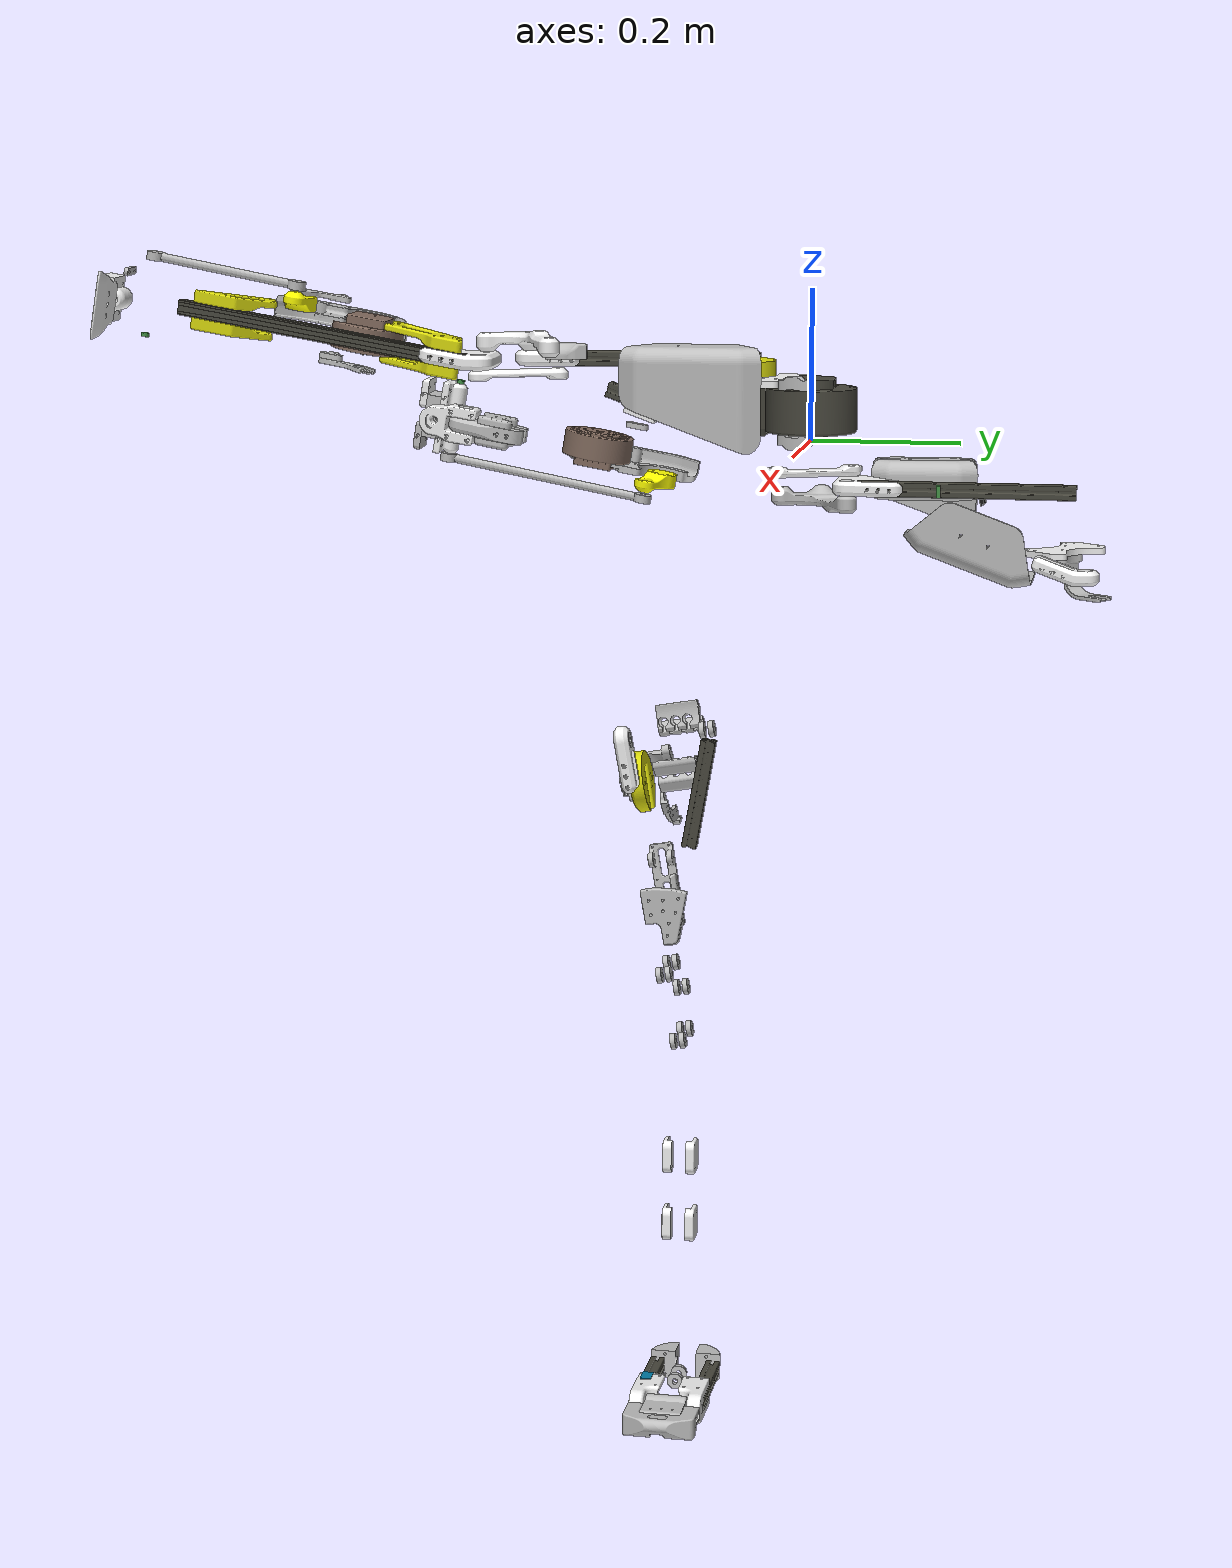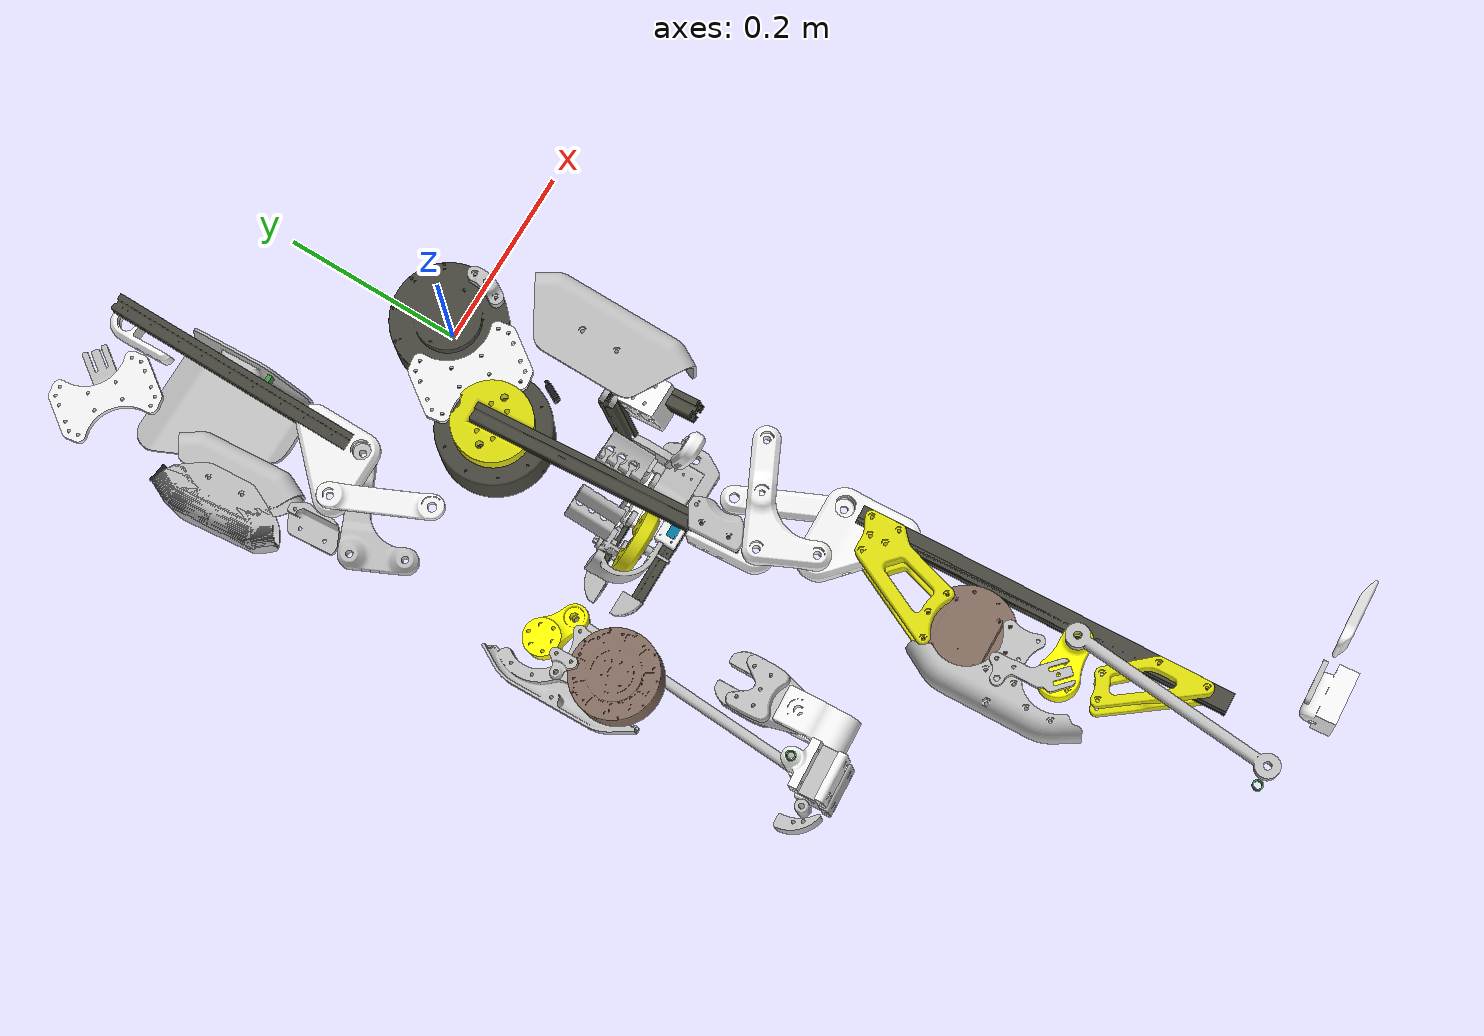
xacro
<?xml version="1.0" ?>
<robot name="humanoidrightleg" xmlns:xacro="http://www.ros.org/wiki/xacro">

<xacro:include filename="$(find humanoidrightleg_description)/urdf/materials.xacro" />
<xacro:include filename="$(find humanoidrightleg_description)/urdf/humanoidrightleg.trans" />
<link name="base_link">
  <inertial>
    <origin xyz="-2.137404171899072e-14 0 0.005" rpy="0 0 0"/>
    <mass value="0.15083462441733"/>
    <inertia ixx="2.21517549468842e-05" iyy="3.39267549369311e-05" izz="5.35645994768598e-05" ixy="0" iyz="0" ixz="3.081487911019577e-33"/>
  </inertial>
  <visual>
    <origin xyz="0 0 0" rpy="0 0 0"/>
    <geometry>
      <mesh filename="package://humanoidrightleg_description/meshes/base_link.stl" scale="0.001 0.001 0.001"/>
    </geometry>
    <material name="steel_satin"/>
  </visual>
  <collision>
    <origin xyz="0 0 0" rpy="0 0 0"/>
    <geometry>
      <mesh filename="package://humanoidrightleg_description/meshes/base_link.stl" scale="0.001 0.001 0.001"/>
    </geometry>
  </collision>
</link>

<link name="RMD-X10-S2_MIR4__3_Stator_1">
  <inertial>
    <origin xyz="-1.1561410892626987e-08 0.0007996823934559865 0.03182069992246948" rpy="0 0 0"/>
    <mass value="1.55306904844425"/>
    <inertia ixx="0.00285644715024274" iyy="0.00292757747778099" izz="0.00369780684183897" ixy="7.224771163531730e-11" iyz="1.67010427996743e-05" ixz="4.91373014642689e-10"/>
  </inertial>
  <visual>
    <origin xyz="-0.0 -0.0 -0.01" rpy="0 0 0"/>
    <geometry>
      <mesh filename="package://humanoidrightleg_description/meshes/RMD-X10-S2_MIR4__3_Stator_1.stl" scale="0.001 0.001 0.001"/>
    </geometry>
    <material name="opaque727161"/>
  </visual>
  <collision>
    <origin xyz="-0.0 -0.0 -0.01" rpy="0 0 0"/>
    <geometry>
      <mesh filename="package://humanoidrightleg_description/meshes/RMD-X10-S2_MIR4__3_Stator_1.stl" scale="0.001 0.001 0.001"/>
    </geometry>
  </collision>
</link>

<link name="leg-pitch-elastic__1__1">
  <inertial>
    <origin xyz="0.0043331749249106155 0.00111244839801433 0.028315467914110406" rpy="0 0 0"/>
    <mass value="0.0245291042760104"/>
    <inertia ixx="9.8175039693855e-06" iyy="8.21623306395601e-06" izz="2.92015853283537e-06" ixy="4.21998763905152e-07" iyz="-2.69850308691085e-07" ixz="9.97190866763669e-08"/>
  </inertial>
  <visual>
    <origin xyz="0.071138 0.011355 -0.012" rpy="0 0 0"/>
    <geometry>
      <mesh filename="package://humanoidrightleg_description/meshes/leg-pitch-elastic__1__1.stl" scale="0.001 0.001 0.001"/>
    </geometry>
    <material name="opaque191191191"/>
  </visual>
  <collision>
    <origin xyz="0.071138 0.011355 -0.012" rpy="0 0 0"/>
    <geometry>
      <mesh filename="package://humanoidrightleg_description/meshes/leg-pitch-elastic__1__1.stl" scale="0.001 0.001 0.001"/>
    </geometry>
  </collision>
</link>

<link name="leg-pitch-elastic__3__1">
  <inertial>
    <origin xyz="0.00028161841037692426 -0.004464786595415545 0.030684539200331342" rpy="0 0 0"/>
    <mass value="0.0245291042760104"/>
    <inertia ixx="8.121096179216e-06" iyy="9.91264085412532e-06" izz="2.9201585328353e-06" ixy="-1.2919753996385e-07" iyz="1.1450155860264e-08" ixz="-2.87457786952056e-07"/>
  </inertial>
  <visual>
    <origin xyz="0.082894 0.027535 -0.012" rpy="0 0 0"/>
    <geometry>
      <mesh filename="package://humanoidrightleg_description/meshes/leg-pitch-elastic__3__1.stl" scale="0.001 0.001 0.001"/>
    </geometry>
    <material name="opaque191191191"/>
  </visual>
  <collision>
    <origin xyz="0.082894 0.027535 -0.012" rpy="0 0 0"/>
    <geometry>
      <mesh filename="package://humanoidrightleg_description/meshes/leg-pitch-elastic__3__1.stl" scale="0.001 0.001 0.001"/>
    </geometry>
  </collision>
</link>

<link name="leg-pitch-elastic__2__1">
  <inertial>
    <origin xyz="-0.000281419190083107 0.004464713281593341 0.030684532085865125" rpy="0 0 0"/>
    <mass value="0.0245291042760104"/>
    <inertia ixx="8.12109617921613e-06" iyy="9.9126408541253e-06" izz="2.92015853283526e-06" ixy="-1.29197539963853e-07" iyz="-1.14501558602572e-08" ixz="2.87457786951236e-07"/>
  </inertial>
  <visual>
    <origin xyz="-0.011184 0.071165 -0.012" rpy="0 0 0"/>
    <geometry>
      <mesh filename="package://humanoidrightleg_description/meshes/leg-pitch-elastic__2__1.stl" scale="0.001 0.001 0.001"/>
    </geometry>
    <material name="opaque191191191"/>
  </visual>
  <collision>
    <origin xyz="-0.011184 0.071165 -0.012" rpy="0 0 0"/>
    <geometry>
      <mesh filename="package://humanoidrightleg_description/meshes/leg-pitch-elastic__2__1.stl" scale="0.001 0.001 0.001"/>
    </geometry>
  </collision>
</link>

<link name="leg-pitch-elastic_1">
  <inertial>
    <origin xyz="-0.00433297570461362 -0.0011125217118188452 0.02831546079961827" rpy="0 0 0"/>
    <mass value="0.0245291042760104"/>
    <inertia ixx="9.81750396938545e-06" iyy="8.21623306395594e-06" izz="2.92015853283533e-06" ixy="4.21998763905183e-07" iyz="2.69850308691019e-07" ixz="-9.97190866774748e-08"/>
  </inertial>
  <visual>
    <origin xyz="0.000572 0.087345 -0.012" rpy="0 0 0"/>
    <geometry>
      <mesh filename="package://humanoidrightleg_description/meshes/leg-pitch-elastic_1.stl" scale="0.001 0.001 0.001"/>
    </geometry>
    <material name="opaque191191191"/>
  </visual>
  <collision>
    <origin xyz="0.000572 0.087345 -0.012" rpy="0 0 0"/>
    <geometry>
      <mesh filename="package://humanoidrightleg_description/meshes/leg-pitch-elastic_1.stl" scale="0.001 0.001 0.001"/>
    </geometry>
  </collision>
</link>

<link name="hip-motor-bracket-v5-right_MIR_1">
  <inertial>
    <origin xyz="0.017145099610158858 -0.04935003665687157 -0.004500000000001279" rpy="0 0 0"/>
    <mass value="0.0629963904640038"/>
    <inertia ixx="4.19044655038384e-05" iyy="6.2878187218024e-05" izz="0.000103932201450599" ixy="3.22752390165202e-05" iyz="-2.286988957586611e-18" ixz="4.397795062144327e-18"/>
  </inertial>
  <visual>
    <origin xyz="0.053 0.0 -0.012" rpy="0 0 0"/>
    <geometry>
      <mesh filename="package://humanoidrightleg_description/meshes/hip-motor-bracket-v5-right_MIR_1.stl" scale="0.001 0.001 0.001"/>
    </geometry>
    <material name="opaque245245245"/>
  </visual>
  <collision>
    <origin xyz="0.053 0.0 -0.012" rpy="0 0 0"/>
    <geometry>
      <mesh filename="package://humanoidrightleg_description/meshes/hip-motor-bracket-v5-right_MIR_1.stl" scale="0.001 0.001 0.001"/>
    </geometry>
  </collision>
</link>

<link name="innner-thigh-magnet-encoder__1__1">
  <inertial>
    <origin xyz="0.018384650368951743 -0.002568109841095942 -0.02778155630905323" rpy="0 0 0"/>
    <mass value="0.0278904055568687"/>
    <inertia ixx="1.76659445346298e-05" iyy="1.5985340031158e-05" izz="1.10005716364315e-05" ixy="-2.56247035072647e-06" iyz="6.12320058242576e-06" ixz="4.44219697098464e-06"/>
  </inertial>
  <visual>
    <origin xyz="0.042878 0.031153 -0.003" rpy="0 0 0"/>
    <geometry>
      <mesh filename="package://humanoidrightleg_description/meshes/innner-thigh-magnet-encoder__1__1.stl" scale="0.001 0.001 0.001"/>
    </geometry>
    <material name="opaque191191191"/>
  </visual>
  <collision>
    <origin xyz="0.042878 0.031153 -0.003" rpy="0 0 0"/>
    <geometry>
      <mesh filename="package://humanoidrightleg_description/meshes/innner-thigh-magnet-encoder__1__1.stl" scale="0.001 0.001 0.001"/>
    </geometry>
  </collision>
</link>

<link name="knee-bend-motor-bracket-hip_1">
  <inertial>
    <origin xyz="-0.0038111444447288256 -0.01598260549680081 -0.008478998621304334" rpy="0 0 0"/>
    <mass value="0.0107277558839088"/>
    <inertia ixx="1.93139707619719e-06" iyy="6.52187217630501e-07" izz="2.10236783725592e-06" ixy="-4.64701319342865e-07" iyz="-7.37049479173783e-09" ixz="2.26759346512173e-08"/>
  </inertial>
  <visual>
    <origin xyz="-0.053 -0.0 -0.012" rpy="0 0 0"/>
    <geometry>
      <mesh filename="package://humanoidrightleg_description/meshes/knee-bend-motor-bracket-hip_1.stl" scale="0.001 0.001 0.001"/>
    </geometry>
    <material name="opaque191191191"/>
  </visual>
  <collision>
    <origin xyz="-0.053 -0.0 -0.012" rpy="0 0 0"/>
    <geometry>
      <mesh filename="package://humanoidrightleg_description/meshes/knee-bend-motor-bracket-hip_1.stl" scale="0.001 0.001 0.001"/>
    </geometry>
  </collision>
</link>

<link name="knee-bend-motor-bracket-hip__1__1">
  <inertial>
    <origin xyz="-0.0038110401177033695 -0.015982284411230948 0.00847899862130437" rpy="0 0 0"/>
    <mass value="0.0107277558839088"/>
    <inertia ixx="1.93139815764031e-06" iyy="6.52186136187552e-07" izz="2.10236783725603e-06" ixy="-4.64699830864174e-07" iyz="7.36572442646488e-09" ixz="-2.26774846368458e-08"/>
  </inertial>
  <visual>
    <origin xyz="-0.053 -0.0 -0.071" rpy="0 0 0"/>
    <geometry>
      <mesh filename="package://humanoidrightleg_description/meshes/knee-bend-motor-bracket-hip__1__1.stl" scale="0.001 0.001 0.001"/>
    </geometry>
    <material name="opaque191191191"/>
  </visual>
  <collision>
    <origin xyz="-0.053 -0.0 -0.071" rpy="0 0 0"/>
    <geometry>
      <mesh filename="package://humanoidrightleg_description/meshes/knee-bend-motor-bracket-hip__1__1.stl" scale="0.001 0.001 0.001"/>
    </geometry>
  </collision>
</link>

<link name="RMD-X10-S2_MIR4Stator_1">
  <inertial>
    <origin xyz="0.01637821078173142 -0.04960639092028741 0.02917930007753167" rpy="0 0 0"/>
    <mass value="1.55306904844426"/>
    <inertia ixx="0.00285644715024275" iyy="0.00292757747778099" izz="0.00369780684183896" ixy="-7.224770955105431e-11" iyz="-1.67010427996753e-05" ixz="4.91373074174017e-10"/>
  </inertial>
  <visual>
    <origin xyz="0.088088 0.048294 -0.012" rpy="0 0 0"/>
    <geometry>
      <mesh filename="package://humanoidrightleg_description/meshes/RMD-X10-S2_MIR4Stator_1.stl" scale="0.001 0.001 0.001"/>
    </geometry>
    <material name="opaque727161"/>
  </visual>
  <collision>
    <origin xyz="0.088088 0.048294 -0.012" rpy="0 0 0"/>
    <geometry>
      <mesh filename="package://humanoidrightleg_description/meshes/RMD-X10-S2_MIR4Stator_1.stl" scale="0.001 0.001 0.001"/>
    </geometry>
  </collision>
</link>

<link name="RMD-X10-S2_MIR4Rotor_1">
  <inertial>
    <origin xyz="-2.1161672708047696e-06 1.6410298648822375e-05 -0.011165974681643147" rpy="0 0 0"/>
    <mass value="0.236112274637419"/>
    <inertia ixx="5.68531155036552e-05" iyy="5.7336639638052e-05" izz="7.49151450519106e-05" ixy="-6.93161398973574e-08" iyz="-2.3024874127751e-08" ixz="3.23928483927753e-09"/>
  </inertial>
  <visual>
    <origin xyz="0.07171 0.0987 -0.073" rpy="0 0 0"/>
    <geometry>
      <mesh filename="package://humanoidrightleg_description/meshes/RMD-X10-S2_MIR4Rotor_1.stl" scale="0.001 0.001 0.001"/>
    </geometry>
    <material name="opaque727161"/>
  </visual>
  <collision>
    <origin xyz="0.07171 0.0987 -0.073" rpy="0 0 0"/>
    <geometry>
      <mesh filename="package://humanoidrightleg_description/meshes/RMD-X10-S2_MIR4Rotor_1.stl" scale="0.001 0.001 0.001"/>
    </geometry>
  </collision>
</link>

<link name="thigh-outer-encoder-mount__1__1">
  <inertial>
    <origin xyz="0.012347854634024116 0.013208765079570972 0.032156691836600845" rpy="0 0 0"/>
    <mass value="0.0298095431336914"/>
    <inertia ixx="1.94825595458806e-05" iyy="2.41201920848334e-05" izz="1.15362961084242e-05" ixy="1.68477718283047e-06" iyz="2.74493604757647e-06" ixz="-8.44793203533018e-06"/>
  </inertial>
  <visual>
    <origin xyz="0.12471 0.0987 -0.071" rpy="0 0 0"/>
    <geometry>
      <mesh filename="package://humanoidrightleg_description/meshes/thigh-outer-encoder-mount__1__1.stl" scale="0.001 0.001 0.001"/>
    </geometry>
    <material name="opaque191191191"/>
  </visual>
  <collision>
    <origin xyz="0.12471 0.0987 -0.071" rpy="0 0 0"/>
    <geometry>
      <mesh filename="package://humanoidrightleg_description/meshes/thigh-outer-encoder-mount__1__1.stl" scale="0.001 0.001 0.001"/>
    </geometry>
  </collision>
</link>

<link name="limit-bracket-knee_1">
  <inertial>
    <origin xyz="0.038087477180112975 0.00807344983971442 0.00200543257018429" rpy="0 0 0"/>
    <mass value="0.0111496094135345"/>
    <inertia ixx="2.38308173316804e-06" iyy="7.30358139373011e-06" izz="9.59027505735826e-06" ixy="-3.43104983657425e-06" iyz="-2.22510402278926e-08" ixz="9.00308746571408e-09"/>
  </inertial>
  <visual>
    <origin xyz="0.088088 0.149106 -0.071" rpy="0 0 0"/>
    <geometry>
      <mesh filename="package://humanoidrightleg_description/meshes/limit-bracket-knee_1.stl" scale="0.001 0.001 0.001"/>
    </geometry>
    <material name="opaque191191191"/>
  </visual>
  <collision>
    <origin xyz="0.088088 0.149106 -0.071" rpy="0 0 0"/>
    <geometry>
      <mesh filename="package://humanoidrightleg_description/meshes/limit-bracket-knee_1.stl" scale="0.001 0.001 0.001"/>
    </geometry>
  </collision>
</link>

<link name="hip-motor-bracket-v5-right_MIR__1__1">
  <inertial>
    <origin xyz="0.02831909901748353 -0.047580037015949136 0.004499999933483212" rpy="0 0 0"/>
    <mass value="0.0629963904640038"/>
    <inertia ixx="4.19044662888547e-05" iyy="6.28781864330074e-05" izz="0.000103932201450599" ixy="3.22752392715876e-05" iyz="-3.294155855211589e-14" ixz="-8.834716270188225e-14"/>
  </inertial>
  <visual>
    <origin xyz="0.064174 0.00177 -0.071" rpy="0 0 0"/>
    <geometry>
      <mesh filename="package://humanoidrightleg_description/meshes/hip-motor-bracket-v5-right_MIR__1__1.stl" scale="0.001 0.001 0.001"/>
    </geometry>
    <material name="opaque245245245"/>
  </visual>
  <collision>
    <origin xyz="0.064174 0.00177 -0.071" rpy="0 0 0"/>
    <geometry>
      <mesh filename="package://humanoidrightleg_description/meshes/hip-motor-bracket-v5-right_MIR__1__1.stl" scale="0.001 0.001 0.001"/>
    </geometry>
  </collision>
</link>

<link name="NO-NC_Bump_Switch__1__1">
  <inertial>
    <origin xyz="0.0006098597083060778 -0.005605907200915444 0.0033312733839520187" rpy="0 0 0"/>
    <mass value="0.00155039406540348"/>
    <inertia ixx="7.02105776941548e-08" iyy="4.0851523004421e-08" izz="6.23354983706727e-08" ixy="-2.17632942777091e-08" iyz="-6.72541221178337e-09" ixz="-3.57596510481949e-09"/>
  </inertial>
  <visual>
    <origin xyz="0.011323 0.125712 -0.06881" rpy="0 0 0"/>
    <geometry>
      <mesh filename="package://humanoidrightleg_description/meshes/NO-NC_Bump_Switch__1__1.stl" scale="0.001 0.001 0.001"/>
    </geometry>
    <material name="opaque252525"/>
  </visual>
  <collision>
    <origin xyz="0.011323 0.125712 -0.06881" rpy="0 0 0"/>
    <geometry>
      <mesh filename="package://humanoidrightleg_description/meshes/NO-NC_Bump_Switch__1__1.stl" scale="0.001 0.001 0.001"/>
    </geometry>
  </collision>
</link>

<link name="NO-NC_Bump_Switch_1">
  <inertial>
    <origin xyz="0.004177517614909906 -0.003788104538661019 0.003331273383956626" rpy="0 0 0"/>
    <mass value="0.00155039406540348"/>
    <inertia ixx="3.02967040915035e-08" iyy="8.07653966070994e-08" izz="6.23354983707032e-08" ixy="7.23583235206848e-09" iyz="-1.06008157257925e-09" ixz="7.54287232483715e-09"/>
  </inertial>
  <visual>
    <origin xyz="0.085847 0.163362 -0.06881" rpy="0 0 0"/>
    <geometry>
      <mesh filename="package://humanoidrightleg_description/meshes/NO-NC_Bump_Switch_1.stl" scale="0.001 0.001 0.001"/>
    </geometry>
    <material name="opaque252525"/>
  </visual>
  <collision>
    <origin xyz="0.085847 0.163362 -0.06881" rpy="0 0 0"/>
    <geometry>
      <mesh filename="package://humanoidrightleg_description/meshes/NO-NC_Bump_Switch_1.stl" scale="0.001 0.001 0.001"/>
    </geometry>
  </collision>
</link>

<link name="hip-ex-al-base_MIR_1">
  <inertial>
    <origin xyz="-9.949334274853006e-06 0.00014878773576262883 0.013372003753055584" rpy="0 0 0"/>
    <mass value="0.145590268667055"/>
    <inertia ixx="7.31142837610502e-05" iyy="8.03439498425385e-05" izz="0.000138206755307654" ixy="-4.95170279436914e-07" iyz="-1.74096248714692e-06" ixz="1.18687228429994e-07"/>
  </inertial>
  <visual>
    <origin xyz="0.07171 0.0987 -0.073" rpy="0 0 0"/>
    <geometry>
      <mesh filename="package://humanoidrightleg_description/meshes/hip-ex-al-base_MIR_1.stl" scale="0.001 0.001 0.001"/>
    </geometry>
    <material name="opaque22122113"/>
  </visual>
  <collision>
    <origin xyz="0.07171 0.0987 -0.073" rpy="0 0 0"/>
    <geometry>
      <mesh filename="package://humanoidrightleg_description/meshes/hip-ex-al-base_MIR_1.stl" scale="0.001 0.001 0.001"/>
    </geometry>
  </collision>
</link>

<link name="motorcap-KNEE_MIR_1">
  <inertial>
    <origin xyz="-0.00010458296907729647 0.001536971231776929 0.010431913725907738" rpy="0 0 0"/>
    <mass value="0.10890019522501"/>
    <inertia ixx="5.28935639643557e-05" iyy="5.74293989570557e-05" izz="0.000103470968365381" ixy="-3.10665335403418e-07" iyz="9.03944422473183e-07" ixz="-6.16246300980637e-08"/>
  </inertial>
  <visual>
    <origin xyz="0.07171 0.0987 -0.1" rpy="0 0 0"/>
    <geometry>
      <mesh filename="package://humanoidrightleg_description/meshes/motorcap-KNEE_MIR_1.stl" scale="0.001 0.001 0.001"/>
    </geometry>
    <material name="opaque22122113"/>
  </visual>
  <collision>
    <origin xyz="0.07171 0.0987 -0.1" rpy="0 0 0"/>
    <geometry>
      <mesh filename="package://humanoidrightleg_description/meshes/motorcap-KNEE_MIR_1.stl" scale="0.001 0.001 0.001"/>
    </geometry>
  </collision>
</link>

<link name="2020_300mm__1__1">
  <inertial>
    <origin xyz="0.0002251870068053774 -0.15033302956237268 -0.00999999999999844" rpy="0 0 0"/>
    <mass value="0.158693154300952"/>
    <inertia ixx="0.00119118913093242" iyy="1.84090653089298e-05" izz="0.0011966651702521" ixy="8.03254427837138e-05" iyz="1.734723475976807e-17" ixz="1.517883041479706e-18"/>
  </inertial>
  <visual>
    <origin xyz="0.063093 0.078066 -0.11" rpy="0 0 0"/>
    <geometry>
      <mesh filename="package://humanoidrightleg_description/meshes/2020_300mm__1__1.stl" scale="0.001 0.001 0.001"/>
    </geometry>
    <material name="opaque727161"/>
  </visual>
  <collision>
    <origin xyz="0.063093 0.078066 -0.11" rpy="0 0 0"/>
    <geometry>
      <mesh filename="package://humanoidrightleg_description/meshes/2020_300mm__1__1.stl" scale="0.001 0.001 0.001"/>
    </geometry>
  </collision>
</link>

<link name="magmount__1__1">
  <inertial>
    <origin xyz="0.0010243448796543597 -0.015026719714054629 0.0058836177326532235" rpy="0 0 0"/>
    <mass value="0.00255116192587274"/>
    <inertia ixx="3.66767669662907e-07" iyy="4.17036722139509e-08" izz="3.71963330959308e-07" ixy="2.22645202741242e-08" iyz="4.86291754897539e-10" ixz="-3.304474641984442e-11"/>
  </inertial>
  <visual>
    <origin xyz="0.072368 0.089044 -0.12" rpy="0 0 0"/>
    <geometry>
      <mesh filename="package://humanoidrightleg_description/meshes/magmount__1__1.stl" scale="0.001 0.001 0.001"/>
    </geometry>
    <material name="opaque191191191"/>
  </visual>
  <collision>
    <origin xyz="0.072368 0.089044 -0.12" rpy="0 0 0"/>
    <geometry>
      <mesh filename="package://humanoidrightleg_description/meshes/magmount__1__1.stl" scale="0.001 0.001 0.001"/>
    </geometry>
  </collision>
</link>

<link name="multiplex-stack_1">
  <inertial>
    <origin xyz="-0.007433506116334768 0.1283988562731877 0.008250058450145217" rpy="0 0 0"/>
    <mass value="0.0312705104814396"/>
    <inertia ixx="4.73909097792112e-05" iyy="6.20786503624759e-06" izz="4.44353789591304e-05" ixy="2.73064384202955e-06" iyz="-3.893434815001318e-11" ixz="1.679204811224494e-11"/>
  </inertial>
  <visual>
    <origin xyz="0.062642 0.378732 -0.09175" rpy="0 0 0"/>
    <geometry>
      <mesh filename="package://humanoidrightleg_description/meshes/multiplex-stack_1.stl" scale="0.001 0.001 0.001"/>
    </geometry>
    <material name="opaque191191191"/>
  </visual>
  <collision>
    <origin xyz="0.062642 0.378732 -0.09175" rpy="0 0 0"/>
    <geometry>
      <mesh filename="package://humanoidrightleg_description/meshes/multiplex-stack_1.stl" scale="0.001 0.001 0.001"/>
    </geometry>
  </collision>
</link>

<link name="thigh-nub_1">
  <inertial>
    <origin xyz="-0.0002645606062967251 0.12517110412256427 -0.00293685000628173" rpy="0 0 0"/>
    <mass value="0.00472150536182149"/>
    <inertia ixx="6.32740393312283e-07" iyy="1.44190787926687e-07" izz="7.43797851447605e-07" ixy="3.34612590436874e-08" iyz="3.290472278330570e-15" ixz="-1.027749120616900e-15"/>
  </inertial>
  <visual>
    <origin xyz="0.060896 0.378613 -0.09" rpy="0 0 0"/>
    <geometry>
      <mesh filename="package://humanoidrightleg_description/meshes/thigh-nub_1.stl" scale="0.001 0.001 0.001"/>
    </geometry>
    <material name="opaque191191191"/>
  </visual>
  <collision>
    <origin xyz="0.060896 0.378613 -0.09" rpy="0 0 0"/>
    <geometry>
      <mesh filename="package://humanoidrightleg_description/meshes/thigh-nub_1.stl" scale="0.001 0.001 0.001"/>
    </geometry>
  </collision>
</link>

<link name="knee-lock-2-b_1">
  <inertial>
    <origin xyz="0.014305292755104386 0.03576491432701612 -0.0029994325015807732" rpy="0 0 0"/>
    <mass value="0.0249396624379923"/>
    <inertia ixx="8.31656001733889e-06" iyy="2.89674732919067e-06" izz="1.0161957421673e-05" ixy="-7.56922154295989e-07" iyz="-4.22946672865021e-07" ixz="-5.14539806772499e-07"/>
  </inertial>
  <visual>
    <origin xyz="0.060896 0.378613 -0.09" rpy="0 0 0"/>
    <geometry>
      <mesh filename="package://humanoidrightleg_description/meshes/knee-lock-2-b_1.stl" scale="0.001 0.001 0.001"/>
    </geometry>
    <material name="opaque191191191"/>
  </visual>
  <collision>
    <origin xyz="0.060896 0.378613 -0.09" rpy="0 0 0"/>
    <geometry>
      <mesh filename="package://humanoidrightleg_description/meshes/knee-lock-2-b_1.stl" scale="0.001 0.001 0.001"/>
    </geometry>
  </collision>
</link>

<link name="knee-lock-2_1">
  <inertial>
    <origin xyz="0.014305284303430518 0.035764915950466436 0.002999432305522992" rpy="0 0 0"/>
    <mass value="0.0249396527238871"/>
    <inertia ixx="8.31655778445357e-06" iyy="2.89674230939994e-06" izz="1.01619503034794e-05" ixy="-7.56923143618599e-07" iyz="4.22946653130807e-07" ixz="5.14539921998348e-07"/>
  </inertial>
  <visual>
    <origin xyz="0.060896 0.378613 -0.11" rpy="0 0 0"/>
    <geometry>
      <mesh filename="package://humanoidrightleg_description/meshes/knee-lock-2_1.stl" scale="0.001 0.001 0.001"/>
    </geometry>
    <material name="opaque191191191"/>
  </visual>
  <collision>
    <origin xyz="0.060896 0.378613 -0.11" rpy="0 0 0"/>
    <geometry>
      <mesh filename="package://humanoidrightleg_description/meshes/knee-lock-2_1.stl" scale="0.001 0.001 0.001"/>
    </geometry>
  </collision>
</link>

<link name="bearingstrap__1__1">
  <inertial>
    <origin xyz="-0.00043186003423186653 0.006342054694422561 -6.298470175969406e-09" rpy="0 0 0"/>
    <mass value="0.0374882084689638"/>
    <inertia ixx="2.33153418581107e-05" iyy="7.78211601904676e-06" izz="2.89911689620049e-05" ixy="1.0639855694219e-06" iyz="9.193034202804873e-11" ixz="-3.902097449413194e-12"/>
  </inertial>
  <visual>
    <origin xyz="0.052666 0.378052 -0.1" rpy="0 0 0"/>
    <geometry>
      <mesh filename="package://humanoidrightleg_description/meshes/bearingstrap__1__1.stl" scale="0.001 0.001 0.001"/>
    </geometry>
    <material name="opaque245245245"/>
  </visual>
  <collision>
    <origin xyz="0.052666 0.378052 -0.1" rpy="0 0 0"/>
    <geometry>
      <mesh filename="package://humanoidrightleg_description/meshes/bearingstrap__1__1.stl" scale="0.001 0.001 0.001"/>
    </geometry>
  </collision>
</link>

<link name="skateboard-bearing__13__1">
  <inertial>
    <origin xyz="-2.900333667954502e-07 6.44297571961161e-08 0.003500000000001016" rpy="0 0 0"/>
    <mass value="0.0181262042130496"/>
    <inertia ixx="6.94837830293726e-07" iyy="6.94837827466669e-07" izz="1.24164499002051e-06" ixy="1.936385080059111e-16" iyz="-1.084202172485504e-19" ixz="1.355252715606881e-20"/>
  </inertial>
  <visual>
    <origin xyz="0.051645 0.393017 -0.09" rpy="0 0 0"/>
    <geometry>
      <mesh filename="package://humanoidrightleg_description/meshes/skateboard-bearing__13__1.stl" scale="0.001 0.001 0.001"/>
    </geometry>
    <material name="opaque191191191"/>
  </visual>
  <collision>
    <origin xyz="0.051645 0.393017 -0.09" rpy="0 0 0"/>
    <geometry>
      <mesh filename="package://humanoidrightleg_description/meshes/skateboard-bearing__13__1.stl" scale="0.001 0.001 0.001"/>
    </geometry>
  </collision>
</link>

<link name="skateboard-bearing__14__1">
  <inertial>
    <origin xyz="-2.90033366351361e-07 6.442975647447113e-08 -0.003499999999999018" rpy="0 0 0"/>
    <mass value="0.0181262042130496"/>
    <inertia ixx="6.94837830293726e-07" iyy="6.94837827466669e-07" izz="1.24164499002094e-06" ixy="1.935842978972868e-16" iyz="-2.168404344971009e-19" ixz="2.710505431213761e-20"/>
  </inertial>
  <visual>
    <origin xyz="0.051645 0.393017 -0.11" rpy="0 0 0"/>
    <geometry>
      <mesh filename="package://humanoidrightleg_description/meshes/skateboard-bearing__14__1.stl" scale="0.001 0.001 0.001"/>
    </geometry>
    <material name="opaque191191191"/>
  </visual>
  <collision>
    <origin xyz="0.051645 0.393017 -0.11" rpy="0 0 0"/>
    <geometry>
      <mesh filename="package://humanoidrightleg_description/meshes/skateboard-bearing__14__1.stl" scale="0.001 0.001 0.001"/>
    </geometry>
  </collision>
</link>

<link name="conjstraint-knee-test-oute_MIR_1">
  <inertial>
    <origin xyz="0.038822812330706225 0.002017481124563625 0.015679038691609234" rpy="0 0 0"/>
    <mass value="0.101273135369729"/>
    <inertia ixx="0.000118613614318058" iyy="0.000120002336288713" izz="0.000231043376690247" ixy="-8.02267716048421e-05" iyz="-2.25620021461481e-06" ixz="-3.64275185411823e-08"/>
  </inertial>
  <visual>
    <origin xyz="0.051645 0.393017 -0.11" rpy="0 0 0"/>
    <geometry>
      <mesh filename="package://humanoidrightleg_description/meshes/conjstraint-knee-test-oute_MIR_1.stl" scale="0.001 0.001 0.001"/>
    </geometry>
    <material name="opaque245245245"/>
  </visual>
  <collision>
    <origin xyz="0.051645 0.393017 -0.11" rpy="0 0 0"/>
    <geometry>
      <mesh filename="package://humanoidrightleg_description/meshes/conjstraint-knee-test-oute_MIR_1.stl" scale="0.001 0.001 0.001"/>
    </geometry>
  </collision>
</link>

<link name="conjstraint-knee-test-oute_1">
  <inertial>
    <origin xyz="0.03881064100299357 0.00203762845062444 -0.01565558166325888" rpy="0 0 0"/>
    <mass value="0.100828257513441"/>
    <inertia ixx="0.000117821292430709" iyy="0.000119177533079321" izz="0.000229456330725731" ixy="-7.97022655077432e-05" iyz="2.26704383052495e-06" ixz="2.97776144578878e-08"/>
  </inertial>
  <visual>
    <origin xyz="0.051645 0.393017 -0.09" rpy="0 0 0"/>
    <geometry>
      <mesh filename="package://humanoidrightleg_description/meshes/conjstraint-knee-test-oute_1.stl" scale="0.001 0.001 0.001"/>
    </geometry>
    <material name="opaque191191191"/>
  </visual>
  <collision>
    <origin xyz="0.051645 0.393017 -0.09" rpy="0 0 0"/>
    <geometry>
      <mesh filename="package://humanoidrightleg_description/meshes/conjstraint-knee-test-oute_1.stl" scale="0.001 0.001 0.001"/>
    </geometry>
  </collision>
</link>

<link name="skateboard-bearing__15__1">
  <inertial>
    <origin xyz="-4.636356562559563e-09 9.929806359804116e-08 0.004000000000000156" rpy="0 0 0"/>
    <mass value="0.0181262042130496"/>
    <inertia ixx="6.94837827453496e-07" iyy="6.94837830307225e-07" izz="1.24164499002077e-06" ixy="-3.388131789017201e-21" iyz="6.776263578034403e-21" ixz="4.065758146820642e-20"/>
  </inertial>
  <visual>
    <origin xyz="-0.050406 0.016378 -0.0895" rpy="0 0 0"/>
    <geometry>
      <mesh filename="package://humanoidrightleg_description/meshes/skateboard-bearing__15__1.stl" scale="0.001 0.001 0.001"/>
    </geometry>
    <material name="opaque191191191"/>
  </visual>
  <collision>
    <origin xyz="-0.050406 0.016378 -0.0895" rpy="0 0 0"/>
    <geometry>
      <mesh filename="package://humanoidrightleg_description/meshes/skateboard-bearing__15__1.stl" scale="0.001 0.001 0.001"/>
    </geometry>
  </collision>
</link>

<link name="bearingstrap_1">
  <inertial>
    <origin xyz="-0.0001490944286988427 -0.021355826483251888 0.009999993701529125" rpy="0 0 0"/>
    <mass value="0.0374882084689638"/>
    <inertia ixx="2.33871204694359e-05" iyy="7.71033740772667e-06" izz="2.89911689620079e-05" ixy="-1.09360609210104e-07" iyz="-9.196414376549944e-11" ixz="-3.001706332496704e-12"/>
  </inertial>
  <visual>
    <origin xyz="-0.050406 0.016378 -0.09" rpy="0 0 0"/>
    <geometry>
      <mesh filename="package://humanoidrightleg_description/meshes/bearingstrap_1.stl" scale="0.001 0.001 0.001"/>
    </geometry>
    <material name="opaque245245245"/>
  </visual>
  <collision>
    <origin xyz="-0.050406 0.016378 -0.09" rpy="0 0 0"/>
    <geometry>
      <mesh filename="package://humanoidrightleg_description/meshes/bearingstrap_1.stl" scale="0.001 0.001 0.001"/>
    </geometry>
  </collision>
</link>

<link name="skateboard-bearing_1">
  <inertial>
    <origin xyz="-4.6363564237816846e-09 9.929819195023115e-08 -0.003499999999999795" rpy="0 0 0"/>
    <mass value="0.0181262042130496"/>
    <inertia ixx="6.94837827453577e-07" iyy="6.94837830307062e-07" izz="1.24164499002076e-06" ixy="1.992221491942114e-17" iyz="0" ixz="-1.355252715606881e-20"/>
  </inertial>
  <visual>
    <origin xyz="-0.050406 0.016378 -0.11" rpy="0 0 0"/>
    <geometry>
      <mesh filename="package://humanoidrightleg_description/meshes/skateboard-bearing_1.stl" scale="0.001 0.001 0.001"/>
    </geometry>
    <material name="opaque191191191"/>
  </visual>
  <collision>
    <origin xyz="-0.050406 0.016378 -0.11" rpy="0 0 0"/>
    <geometry>
      <mesh filename="package://humanoidrightleg_description/meshes/skateboard-bearing_1.stl" scale="0.001 0.001 0.001"/>
    </geometry>
  </collision>
</link>

<link name="2020_300mm__2__1">
  <inertial>
    <origin xyz="-0.0010469125855224054 -0.14999587976826007 2.1649348980190553e-15" rpy="0 0 0"/>
    <mass value="0.158693154300952"/>
    <inertia ixx="0.00119660747751961" iyy="1.29907187217692e-05" izz="0.00119666517025191" ixy="-8.26374083571515e-06" iyz="3.382710778154774e-17" ixz="7.589415207398531e-19"/>
  </inertial>
  <visual>
    <origin xyz="-0.050301 0.031378 -0.1" rpy="0 0 0"/>
    <geometry>
      <mesh filename="package://humanoidrightleg_description/meshes/2020_300mm__2__1.stl" scale="0.001 0.001 0.001"/>
    </geometry>
    <material name="opaque727161"/>
  </visual>
  <collision>
    <origin xyz="-0.050301 0.031378 -0.1" rpy="0 0 0"/>
    <geometry>
      <mesh filename="package://humanoidrightleg_description/meshes/2020_300mm__2__1.stl" scale="0.001 0.001 0.001"/>
    </geometry>
  </collision>
</link>

<link name="skateboard-bearing__8__1">
  <inertial>
    <origin xyz="-4.6363194602938584e-09 9.929817924858586e-08 -0.00316499999999995" rpy="0 0 0"/>
    <mass value="0.0181262042130496"/>
    <inertia ixx="6.94837828439406e-07" iyy="6.94837829321272e-07" izz="1.24164499002079e-06" ixy="1.357019626334853e-15" iyz="0" ixz="0"/>
  </inertial>
  <visual>
    <origin xyz="-0.050406 0.016378 0.0065" rpy="0 0 0"/>
    <geometry>
      <mesh filename="package://humanoidrightleg_description/meshes/skateboard-bearing__8__1.stl" scale="0.001 0.001 0.001"/>
    </geometry>
    <material name="opaque191191191"/>
  </visual>
  <collision>
    <origin xyz="-0.050406 0.016378 0.0065" rpy="0 0 0"/>
    <geometry>
      <mesh filename="package://humanoidrightleg_description/meshes/skateboard-bearing__8__1.stl" scale="0.001 0.001 0.001"/>
    </geometry>
  </collision>
</link>

<link name="bearingstrap-inner-thigh_1">
  <inertial>
    <origin xyz="-0.00015944949609480313 -0.022838323467475854 -0.004863339606971516" rpy="0 0 0"/>
    <mass value="0.0392594141797221"/>
    <inertia ixx="2.74109330007626e-05" iyy="9.82897014218985e-06" izz="3.17047643490234e-05" ixy="-1.22753234563924e-07" iyz="5.81859333464326e-06" ixz="4.06221045809399e-08"/>
  </inertial>
  <visual>
    <origin xyz="-0.050406 0.016378 0.006165" rpy="0 0 0"/>
    <geometry>
      <mesh filename="package://humanoidrightleg_description/meshes/bearingstrap-inner-thigh_1.stl" scale="0.001 0.001 0.001"/>
    </geometry>
    <material name="opaque245245245"/>
  </visual>
  <collision>
    <origin xyz="-0.050406 0.016378 0.006165" rpy="0 0 0"/>
    <geometry>
      <mesh filename="package://humanoidrightleg_description/meshes/bearingstrap-inner-thigh_1.stl" scale="0.001 0.001 0.001"/>
    </geometry>
  </collision>
</link>

<link name="skateboard-bearing__9__1">
  <inertial>
    <origin xyz="-4.636356049081414e-09 9.929806425376664e-08 0.003500000000000149" rpy="0 0 0"/>
    <mass value="0.0181262042130496"/>
    <inertia ixx="6.94837827453618e-07" iyy="6.94837830307042e-07" izz="1.24164499002077e-06" ixy="1.992052085352664e-17" iyz="4.235164736271502e-21" ixz="-3.388131789017201e-21"/>
  </inertial>
  <visual>
    <origin xyz="-0.050406 0.016378 0.026165" rpy="0 0 0"/>
    <geometry>
      <mesh filename="package://humanoidrightleg_description/meshes/skateboard-bearing__9__1.stl" scale="0.001 0.001 0.001"/>
    </geometry>
    <material name="opaque191191191"/>
  </visual>
  <collision>
    <origin xyz="-0.050406 0.016378 0.026165" rpy="0 0 0"/>
    <geometry>
      <mesh filename="package://humanoidrightleg_description/meshes/skateboard-bearing__9__1.stl" scale="0.001 0.001 0.001"/>
    </geometry>
  </collision>
</link>

<link name="2020_150mm__1___1__1">
  <inertial>
    <origin xyz="-0.010624738793506984 -0.07382500329055633 0.016254510749410044" rpy="0 0 0"/>
    <mass value="0.0793465771504762"/>
    <inertia ixx="0.000152001825021016" iyy="2.3497906820719e-05" izz="0.000134982958463058" ixy="-8.9718489409003e-07" iyz="4.67750208619071e-05" ixz="3.26556554032851e-07"/>
  </inertial>
  <visual>
    <origin xyz="-0.060325 0.028027 0.006768" rpy="0 0 0"/>
    <geometry>
      <mesh filename="package://humanoidrightleg_description/meshes/2020_150mm__1___1__1.stl" scale="0.001 0.001 0.001"/>
    </geometry>
    <material name="opaque727161"/>
  </visual>
  <collision>
    <origin xyz="-0.060325 0.028027 0.006768" rpy="0 0 0"/>
    <geometry>
      <mesh filename="package://humanoidrightleg_description/meshes/2020_150mm__1___1__1.stl" scale="0.001 0.001 0.001"/>
    </geometry>
  </collision>
</link>

<link name="2020_100mm__12__1">
  <inertial>
    <origin xyz="-0.00032776864173092446 -0.04698371843300511 0.017101028665118284" rpy="0 0 0"/>
    <mass value="0.0528977181003175"/>
    <inertia ixx="4.6235131727215e-05" iyy="9.21721486701606e-06" izz="4.13325342332746e-05" ixy="-2.58450608222553e-07" iyz="1.34744049647525e-05" ixz="9.40706208536638e-08"/>
  </inertial>
  <visual>
    <origin xyz="-0.049208 0.172327 -0.035138" rpy="0 0 0"/>
    <geometry>
      <mesh filename="package://humanoidrightleg_description/meshes/2020_100mm__12__1.stl" scale="0.001 0.001 0.001"/>
    </geometry>
    <material name="opaque727161"/>
  </visual>
  <collision>
    <origin xyz="-0.049208 0.172327 -0.035138" rpy="0 0 0"/>
    <geometry>
      <mesh filename="package://humanoidrightleg_description/meshes/2020_100mm__12__1.stl" scale="0.001 0.001 0.001"/>
    </geometry>
  </collision>
</link>

<link name="6band__5__1">
  <inertial>
    <origin xyz="-0.01900539958591812 0.053069920298578654 -0.008808113747868399" rpy="0 0 0"/>
    <mass value="0.044524736884465"/>
    <inertia ixx="1.63878030688181e-05" iyy="1.46022953863863e-05" izz="1.39803520381875e-05" ixy="4.08929445650029e-08" iyz="-1.14458709631971e-07" ixz="-7.19053547071309e-08"/>
  </inertial>
  <visual>
    <origin xyz="-0.056778 0.269772 -0.059943" rpy="0 0 0"/>
    <geometry>
      <mesh filename="package://humanoidrightleg_description/meshes/6band__5__1.stl" scale="0.001 0.001 0.001"/>
    </geometry>
    <material name="opaque245245245"/>
  </visual>
  <collision>
    <origin xyz="-0.056778 0.269772 -0.059943" rpy="0 0 0"/>
    <geometry>
      <mesh filename="package://humanoidrightleg_description/meshes/6band__5__1.stl" scale="0.001 0.001 0.001"/>
    </geometry>
  </collision>
</link>

<link name="leg-thigh-knee-support-bottom_1">
  <inertial>
    <origin xyz="-0.00011664944665303739 -0.015645331178396782 0.008912703587378362" rpy="0 0 0"/>
    <mass value="0.0209986825736295"/>
    <inertia ixx="4.00403645865418e-06" iyy="1.84263893593221e-06" izz="3.59147301600511e-06" ixy="-1.4716645425298e-08" iyz="1.71419252738248e-07" ixz="3.58738758019167e-10"/>
  </inertial>
  <visual>
    <origin xyz="-0.048552 0.266294 -0.06934" rpy="0 0 0"/>
    <geometry>
      <mesh filename="package://humanoidrightleg_description/meshes/leg-thigh-knee-support-bottom_1.stl" scale="0.001 0.001 0.001"/>
    </geometry>
    <material name="opaque191191191"/>
  </visual>
  <collision>
    <origin xyz="-0.048552 0.266294 -0.06934" rpy="0 0 0"/>
    <geometry>
      <mesh filename="package://humanoidrightleg_description/meshes/leg-thigh-knee-support-bottom_1.stl" scale="0.001 0.001 0.001"/>
    </geometry>
  </collision>
</link>

<link name="thigh-bracket_1">
  <inertial>
    <origin xyz="0.005201966424594279 0.03313501561044341 -0.0014204300265370229" rpy="0 0 0"/>
    <mass value="0.038133616798884"/>
    <inertia ixx="2.40121873713089e-05" iyy="8.94352695085987e-06" izz="1.56995184517465e-05" ixy="-1.07540532074128e-07" iyz="-1.08750587908774e-06" ixz="-6.98851844538957e-09"/>
  </inertial>
  <visual>
    <origin xyz="-0.058406 0.287284 -0.082479" rpy="0 0 0"/>
    <geometry>
      <mesh filename="package://humanoidrightleg_description/meshes/thigh-bracket_1.stl" scale="0.001 0.001 0.001"/>
    </geometry>
    <material name="opaque191191191"/>
  </visual>
  <collision>
    <origin xyz="-0.058406 0.287284 -0.082479" rpy="0 0 0"/>
    <geometry>
      <mesh filename="package://humanoidrightleg_description/meshes/thigh-bracket_1.stl" scale="0.001 0.001 0.001"/>
    </geometry>
  </collision>
</link>

<link name="double-bracket_1">
  <inertial>
    <origin xyz="-0.02534227251203961 0.002146310658678152 -1.08977525614673e-09" rpy="0 0 0"/>
    <mass value="0.108429762892375"/>
    <inertia ixx="6.23542759453904e-05" iyy="6.79215069912566e-05" izz="0.000123581064906593" ixy="-1.62861992795238e-05" iyz="-2.156923945006994e-12" ixz="1.580942137185265e-12"/>
  </inertial>
  <visual>
    <origin xyz="-0.048207 0.33137 -0.1" rpy="0 0 0"/>
    <geometry>
      <mesh filename="package://humanoidrightleg_description/meshes/double-bracket_1.stl" scale="0.001 0.001 0.001"/>
    </geometry>
    <material name="opaque245245245"/>
  </visual>
  <collision>
    <origin xyz="-0.048207 0.33137 -0.1" rpy="0 0 0"/>
    <geometry>
      <mesh filename="package://humanoidrightleg_description/meshes/double-bracket_1.stl" scale="0.001 0.001 0.001"/>
    </geometry>
  </collision>
</link>

<link name="skateboard-bearing__11__1">
  <inertial>
    <origin xyz="1.7946537959195874e-07 1.4116536128927493e-07 -0.0034999999999962422" rpy="0 0 0"/>
    <mass value="0.0181262042130496"/>
    <inertia ixx="6.9483783030717e-07" iyy="6.94837827453605e-07" izz="1.24164499002051e-06" ixy="-1.994931997373328e-17" iyz="-1.084202172485504e-19" ixz="1.355252715606881e-20"/>
  </inertial>
  <visual>
    <origin xyz="-0.048102 0.34637 -0.11" rpy="0 0 0"/>
    <geometry>
      <mesh filename="package://humanoidrightleg_description/meshes/skateboard-bearing__11__1.stl" scale="0.001 0.001 0.001"/>
    </geometry>
    <material name="opaque191191191"/>
  </visual>
  <collision>
    <origin xyz="-0.048102 0.34637 -0.11" rpy="0 0 0"/>
    <geometry>
      <mesh filename="package://humanoidrightleg_description/meshes/skateboard-bearing__11__1.stl" scale="0.001 0.001 0.001"/>
    </geometry>
  </collision>
</link>

<link name="skateboard-bearing__20__1">
  <inertial>
    <origin xyz="-3.58379128441097e-07 1.6775523914436263e-08 -0.00349999999999652" rpy="0 0 0"/>
    <mass value="0.0181262042130496"/>
    <inertia ixx="6.94837830306737e-07" iyy="6.94837827453659e-07" izz="1.24164499002008e-06" ixy="-1.993576744657721e-17" iyz="1.084202172485504e-19" ixz="0"/>
  </inertial>
  <visual>
    <origin xyz="0.011896 0.345951 -0.11" rpy="0 0 0"/>
    <geometry>
      <mesh filename="package://humanoidrightleg_description/meshes/skateboard-bearing__20__1.stl" scale="0.001 0.001 0.001"/>
    </geometry>
    <material name="opaque191191191"/>
  </visual>
  <collision>
    <origin xyz="0.011896 0.345951 -0.11" rpy="0 0 0"/>
    <geometry>
      <mesh filename="package://humanoidrightleg_description/meshes/skateboard-bearing__20__1.stl" scale="0.001 0.001 0.001"/>
    </geometry>
  </collision>
</link>

<link name="skateboard-bearing__10__1">
  <inertial>
    <origin xyz="1.7946537984869781e-07 1.411653617888753e-07 0.003500000000003639" rpy="0 0 0"/>
    <mass value="0.0181262042130496"/>
    <inertia ixx="6.9483783030717e-07" iyy="6.94837827453686e-07" izz="1.24164499002051e-06" ixy="-1.994931997373328e-17" iyz="0" ixz="1.355252715606881e-20"/>
  </inertial>
  <visual>
    <origin xyz="-0.048102 0.34637 -0.09" rpy="0 0 0"/>
    <geometry>
      <mesh filename="package://humanoidrightleg_description/meshes/skateboard-bearing__10__1.stl" scale="0.001 0.001 0.001"/>
    </geometry>
    <material name="opaque191191191"/>
  </visual>
  <collision>
    <origin xyz="-0.048102 0.34637 -0.09" rpy="0 0 0"/>
    <geometry>
      <mesh filename="package://humanoidrightleg_description/meshes/skateboard-bearing__10__1.stl" scale="0.001 0.001 0.001"/>
    </geometry>
  </collision>
</link>

<link name="skateboard-bearing__16__1">
  <inertial>
    <origin xyz="-3.583790006422838e-07 1.6775523192791297e-08 0.0035000000000033615" rpy="0 0 0"/>
    <mass value="0.0181262042130496"/>
    <inertia ixx="6.9483783030717e-07" iyy="6.94837827453605e-07" izz="1.24164499002094e-06" ixy="-1.992221491942114e-17" iyz="0" ixz="-3.388131789017201e-21"/>
  </inertial>
  <visual>
    <origin xyz="0.011896 0.345951 -0.09" rpy="0 0 0"/>
    <geometry>
      <mesh filename="package://humanoidrightleg_description/meshes/skateboard-bearing__16__1.stl" scale="0.001 0.001 0.001"/>
    </geometry>
    <material name="opaque191191191"/>
  </visual>
  <collision>
    <origin xyz="0.011896 0.345951 -0.09" rpy="0 0 0"/>
    <geometry>
      <mesh filename="package://humanoidrightleg_description/meshes/skateboard-bearing__16__1.stl" scale="0.001 0.001 0.001"/>
    </geometry>
  </collision>
</link>

<link name="dumXrigid_1">
  <inertial>
    <origin xyz="0.004788118475354965 0.11292328537245563 -0.008977556594237712" rpy="0 0 0"/>
    <mass value="0.0008014552972209"/>
    <inertia ixx="2.12566917905704e-08" iyy="2.38611676080182e-08" izz="5.94412678778087e-09" ixy="1.818385301341941e-11" iyz="3.388131789017201e-21" ixz="-2.541098841762901e-21"/>
  </inertial>
  <visual>
    <origin xyz="-0.058207 0.33144 -0.10825" rpy="0 0 0"/>
    <geometry>
      <mesh filename="package://humanoidrightleg_description/meshes/dumXrigid_1.stl" scale="0.001 0.001 0.001"/>
    </geometry>
    <material name="powder_coat_green"/>
  </visual>
  <collision>
    <origin xyz="-0.058207 0.33144 -0.10825" rpy="0 0 0"/>
    <geometry>
      <mesh filename="package://humanoidrightleg_description/meshes/dumXrigid_1.stl" scale="0.001 0.001 0.001"/>
    </geometry>
  </collision>
</link>

<link name="knee-strap-second-test__1__1">
  <inertial>
    <origin xyz="0.022122012793745295 -0.04831943297277952 0.0060127347956917265" rpy="0 0 0"/>
    <mass value="0.250493639418355"/>
    <inertia ixx="0.000320469897576586" iyy="8.04453297641094e-05" izz="0.000395899642795905" ixy="0.000139035654711198" iyz="-2.09023184373665e-06" ixz="9.56978966311264e-07"/>
  </inertial>
  <visual>
    <origin xyz="0.011896 0.345951 -0.11" rpy="0 0 0"/>
    <geometry>
      <mesh filename="package://humanoidrightleg_description/meshes/knee-strap-second-test__1__1.stl" scale="0.001 0.001 0.001"/>
    </geometry>
    <material name="opaque245245245"/>
  </visual>
  <collision>
    <origin xyz="0.011896 0.345951 -0.11" rpy="0 0 0"/>
    <geometry>
      <mesh filename="package://humanoidrightleg_description/meshes/knee-strap-second-test__1__1.stl" scale="0.001 0.001 0.001"/>
    </geometry>
  </collision>
</link>

<link name="knee-strap-second-test_1">
  <inertial>
    <origin xyz="0.023668157351731813 -0.05169650558353833 -0.006012734795683622" rpy="0 0 0"/>
    <mass value="0.0373347207795511"/>
    <inertia ixx="4.77643158293449e-05" iyy="1.19899282456364e-05" izz="5.9006698353019e-05" ixy="2.07225006974439e-05" iyz="-3.11537300970444e-07" ixz="1.42633492247036e-07"/>
  </inertial>
  <visual>
    <origin xyz="0.011896 0.345951 -0.09" rpy="0 0 0"/>
    <geometry>
      <mesh filename="package://humanoidrightleg_description/meshes/knee-strap-second-test_1.stl" scale="0.001 0.001 0.001"/>
    </geometry>
    <material name="opaque245245245"/>
  </visual>
  <collision>
    <origin xyz="0.011896 0.345951 -0.09" rpy="0 0 0"/>
    <geometry>
      <mesh filename="package://humanoidrightleg_description/meshes/knee-strap-second-test_1.stl" scale="0.001 0.001 0.001"/>
    </geometry>
  </collision>
</link>

<link name="skateboard-bearing__19__1">
  <inertial>
    <origin xyz="-3.868926872693801e-07 -1.3942924020904357e-07 -0.0034999999999952708" rpy="0 0 0"/>
    <mass value="0.0181262042130496"/>
    <inertia ixx="6.9483782794838e-07" iyy="6.94837829812639e-07" izz="1.24164499002051e-06" ixy="-1.080190624447308e-15" iyz="-1.084202172485504e-19" ixz="0"/>
  </inertial>
  <visual>
    <origin xyz="-0.033895 0.445967 -0.11" rpy="0 0 0"/>
    <geometry>
      <mesh filename="package://humanoidrightleg_description/meshes/skateboard-bearing__19__1.stl" scale="0.001 0.001 0.001"/>
    </geometry>
    <material name="opaque191191191"/>
  </visual>
  <collision>
    <origin xyz="-0.033895 0.445967 -0.11" rpy="0 0 0"/>
    <geometry>
      <mesh filename="package://humanoidrightleg_description/meshes/skateboard-bearing__19__1.stl" scale="0.001 0.001 0.001"/>
    </geometry>
  </collision>
</link>

<link name="skateboard-bearing__18__1">
  <inertial>
    <origin xyz="-3.7732879525770313e-07 -1.6031859206844246e-07 0.0035000000000046244" rpy="0 0 0"/>
    <mass value="0.0181262042130496"/>
    <inertia ixx="6.94837827948814e-07" iyy="6.94837829812639e-07" izz="1.24164499002138e-06" ixy="-1.080136414338684e-15" iyz="1.084202172485504e-19" ixz="6.776263578034403e-21"/>
  </inertial>
  <visual>
    <origin xyz="-0.033895 0.445967 -0.09" rpy="0 0 0"/>
    <geometry>
      <mesh filename="package://humanoidrightleg_description/meshes/skateboard-bearing__18__1.stl" scale="0.001 0.001 0.001"/>
    </geometry>
    <material name="opaque191191191"/>
  </visual>
  <collision>
    <origin xyz="-0.033895 0.445967 -0.09" rpy="0 0 0"/>
    <geometry>
      <mesh filename="package://humanoidrightleg_description/meshes/skateboard-bearing__18__1.stl" scale="0.001 0.001 0.001"/>
    </geometry>
  </collision>
</link>

<link name="skateboard-bearing__17__1">
  <inertial>
    <origin xyz="-3.246686476887639e-07 -6.351088943645777e-08 -0.003499999999999337" rpy="0 0 0"/>
    <mass value="0.0181262042130496"/>
    <inertia ixx="6.94837829794126e-07" iyy="6.94837827966947e-07" izz="1.24164499002138e-06" ixy="1.096209711545781e-15" iyz="0" ixz="1.355252715606881e-20"/>
  </inertial>
  <visual>
    <origin xyz="0.026193 0.447351 -0.11" rpy="0 0 0"/>
    <geometry>
      <mesh filename="package://humanoidrightleg_description/meshes/skateboard-bearing__17__1.stl" scale="0.001 0.001 0.001"/>
    </geometry>
    <material name="opaque191191191"/>
  </visual>
  <collision>
    <origin xyz="0.026193 0.447351 -0.11" rpy="0 0 0"/>
    <geometry>
      <mesh filename="package://humanoidrightleg_description/meshes/skateboard-bearing__17__1.stl" scale="0.001 0.001 0.001"/>
    </geometry>
  </collision>
</link>

<link name="skateboard-bearing__12__1">
  <inertial>
    <origin xyz="-3.2466864919797334e-07 -6.35108886037905e-08 0.003500000000000794" rpy="0 0 0"/>
    <mass value="0.0181262042130496"/>
    <inertia ixx="6.94837829792825e-07" iyy="6.94837827967001e-07" izz="1.24164499002051e-06" ixy="1.096209711545781e-15" iyz="-1.084202172485504e-19" ixz="1.355252715606881e-20"/>
  </inertial>
  <visual>
    <origin xyz="0.026193 0.447351 -0.09" rpy="0 0 0"/>
    <geometry>
      <mesh filename="package://humanoidrightleg_description/meshes/skateboard-bearing__12__1.stl" scale="0.001 0.001 0.001"/>
    </geometry>
    <material name="opaque191191191"/>
  </visual>
  <collision>
    <origin xyz="0.026193 0.447351 -0.09" rpy="0 0 0"/>
    <geometry>
      <mesh filename="package://humanoidrightleg_description/meshes/skateboard-bearing__12__1.stl" scale="0.001 0.001 0.001"/>
    </geometry>
  </collision>
</link>

<link name="double-bracket-10deg_MIR_MIR_MIR_1">
  <inertial>
    <origin xyz="-0.025253920609580843 -0.01840912687394991 -0.008320426037824527" rpy="0 0 0"/>
    <mass value="0.114064797607905"/>
    <inertia ixx="6.70276055446326e-05" iyy="7.48318988230774e-05" izz="0.000133189187608948" ixy="1.67579668221702e-05" iyz="6.13978331583803e-06" ixz="-2.40861198577467e-06"/>
  </inertial>
  <visual>
    <origin xyz="-0.033895 0.445967 -0.11" rpy="0 0 0"/>
    <geometry>
      <mesh filename="package://humanoidrightleg_description/meshes/double-bracket-10deg_MIR_MIR_MIR_1.stl" scale="0.001 0.001 0.001"/>
    </geometry>
    <material name="opaque245245245"/>
  </visual>
  <collision>
    <origin xyz="-0.033895 0.445967 -0.11" rpy="0 0 0"/>
    <geometry>
      <mesh filename="package://humanoidrightleg_description/meshes/double-bracket-10deg_MIR_MIR_MIR_1.stl" scale="0.001 0.001 0.001"/>
    </geometry>
  </collision>
</link>

<link name="400mmexal_MIR2_MIR3_1">
  <inertial>
    <origin xyz="0.004811828319462308 -0.19690276920112104 0.03473008260966991" rpy="0 0 0"/>
    <mass value="0.432"/>
    <inertia ixx="0.00577107369032748" iyy="0.000205377348678776" izz="0.00560114896099378" ixy="0.00013610398198269" iyz="0.000982262164898356" ixz="-2.40059702328334e-05"/>
  </inertial>
  <visual>
    <origin xyz="-0.034328 0.463685 -0.100227" rpy="0 0 0"/>
    <geometry>
      <mesh filename="package://humanoidrightleg_description/meshes/400mmexal_MIR2_MIR3_1.stl" scale="0.001 0.001 0.001"/>
    </geometry>
    <material name="opaque727161"/>
  </visual>
  <collision>
    <origin xyz="-0.034328 0.463685 -0.100227" rpy="0 0 0"/>
    <geometry>
      <mesh filename="package://humanoidrightleg_description/meshes/400mmexal_MIR2_MIR3_1.stl" scale="0.001 0.001 0.001"/>
    </geometry>
  </collision>
</link>

<link name="2020_400mm_1">
  <inertial>
    <origin xyz="0.004811828319462419 -0.19690276920111993 0.03473008260966971" rpy="0 0 0"/>
    <mass value="0.21159087240127"/>
    <inertia ixx="0.00282820535220385" iyy="0.000103682286025445" izz="0.00274502369511002" ixy="6.66257042331994e-05" iyz="0.000480837573777482" ixz="-1.17514171831231e-05"/>
  </inertial>
  <visual>
    <origin xyz="-0.034328 0.463685 -0.100227" rpy="0 0 0"/>
    <geometry>
      <mesh filename="package://humanoidrightleg_description/meshes/2020_400mm_1.stl" scale="0.001 0.001 0.001"/>
    </geometry>
    <material name="opaque727161"/>
  </visual>
  <collision>
    <origin xyz="-0.034328 0.463685 -0.100227" rpy="0 0 0"/>
    <geometry>
      <mesh filename="package://humanoidrightleg_description/meshes/2020_400mm_1.stl" scale="0.001 0.001 0.001"/>
    </geometry>
  </collision>
</link>

<link name="motor-calf-exal-mount_4">
  <inertial>
    <origin xyz="-0.0017880251806005193 -0.14985476506531725 0.018979165189555336" rpy="0 0 0"/>
    <mass value="0.016630111988706"/>
    <inertia ixx="2.79997338240284e-06" iyy="1.98324604993151e-06" izz="4.21976247245732e-06" ixy="-2.17982072853217e-08" iyz="4.00827894601625e-07" ixz="-2.46476262492454e-07"/>
  </inertial>
  <visual>
    <origin xyz="-0.03437 0.465421 -0.090379" rpy="0 0 0"/>
    <geometry>
      <mesh filename="package://humanoidrightleg_description/meshes/motor-calf-exal-mount_4.stl" scale="0.001 0.001 0.001"/>
    </geometry>
    <material name="opaque245245245"/>
  </visual>
  <collision>
    <origin xyz="-0.03437 0.465421 -0.090379" rpy="0 0 0"/>
    <geometry>
      <mesh filename="package://humanoidrightleg_description/meshes/motor-calf-exal-mount_4.stl" scale="0.001 0.001 0.001"/>
    </geometry>
  </collision>
</link>

<link name="motor-calf-exal-mount_3">
  <inertial>
    <origin xyz="-0.0018499566426174174 -0.1473147099568401 0.033388405085930786" rpy="0 0 0"/>
    <mass value="0.016630111988706"/>
    <inertia ixx="2.79589729368715e-06" iyy="1.98732213864888e-06" izz="4.21976247245905e-06" ixy="6.15434838684083e-08" iyz="4.12389669828938e-07" ixz="2.26601653307505e-07"/>
  </inertial>
  <visual>
    <origin xyz="-0.034285 0.461949 -0.110076" rpy="0 0 0"/>
    <geometry>
      <mesh filename="package://humanoidrightleg_description/meshes/motor-calf-exal-mount_3.stl" scale="0.001 0.001 0.001"/>
    </geometry>
    <material name="opaque245245245"/>
  </visual>
  <collision>
    <origin xyz="-0.034285 0.461949 -0.110076" rpy="0 0 0"/>
    <geometry>
      <mesh filename="package://humanoidrightleg_description/meshes/motor-calf-exal-mount_3.stl" scale="0.001 0.001 0.001"/>
    </geometry>
  </collision>
</link>

<link name="RMD-X8-Pro_MIR8_MIR1_2">
  <inertial>
    <origin xyz="-0.040134192727816195 -0.010479800929352301 0.02135473249099888" rpy="0 0 0"/>
    <mass value="0.516851847486673"/>
    <inertia ixx="0.000498655642010959" iyy="0.000513535052077723" izz="0.00072913909135594" ixy="6.47139426877483e-07" iyz="3.94076564210963e-05" ixz="4.84452254270133e-06"/>
  </inertial>
  <visual>
    <origin xyz="-0.018723 0.602861 -0.106923" rpy="0 0 0"/>
    <geometry>
      <mesh filename="package://humanoidrightleg_description/meshes/RMD-X8-Pro_MIR8_MIR1_2.stl" scale="0.001 0.001 0.001"/>
    </geometry>
    <material name="opaque13110895"/>
  </visual>
  <collision>
    <origin xyz="-0.018723 0.602861 -0.106923" rpy="0 0 0"/>
    <geometry>
      <mesh filename="package://humanoidrightleg_description/meshes/RMD-X8-Pro_MIR8_MIR1_2.stl" scale="0.001 0.001 0.001"/>
    </geometry>
  </collision>
</link>

<link name="calf-skin_1">
  <inertial>
    <origin xyz="0.026223945266112585 0.052342436686971805 -0.007360582275313138" rpy="0 0 0"/>
    <mass value="0.0703660332455744"/>
    <inertia ixx="6.85071202707298e-05" iyy="4.08648858447316e-05" izz="0.000100410099875214" ixy="-2.99296626007804e-05" iyz="1.42605589293372e-05" ixz="6.64293989723257e-06"/>
  </inertial>
  <visual>
    <origin xyz="0.022026 0.569272 -0.136367" rpy="0 0 0"/>
    <geometry>
      <mesh filename="package://humanoidrightleg_description/meshes/calf-skin_1.stl" scale="0.001 0.001 0.001"/>
    </geometry>
    <material name="opaque22122113"/>
  </visual>
  <collision>
    <origin xyz="0.022026 0.569272 -0.136367" rpy="0 0 0"/>
    <geometry>
      <mesh filename="package://humanoidrightleg_description/meshes/calf-skin_1.stl" scale="0.001 0.001 0.001"/>
    </geometry>
  </collision>
</link>

<link name="calf-skin_flip_1">
  <inertial>
    <origin xyz="0.026239299630885872 0.051742866277586064 -0.010761423124110492" rpy="0 0 0"/>
    <mass value="0.0703660332452003"/>
    <inertia ixx="6.85324861703154e-05" iyy="3.85725795080967e-05" izz="0.000102677040311888" ixy="-3.04206046941803e-05" iyz="7.95826208220291e-06" ixz="3.69404663076464e-06"/>
  </inertial>
  <visual>
    <origin xyz="0.021967 0.57535 -0.101899" rpy="0 0 0"/>
    <geometry>
      <mesh filename="package://humanoidrightleg_description/meshes/calf-skin_flip_1.stl" scale="0.001 0.001 0.001"/>
    </geometry>
    <material name="opaque22122113"/>
  </visual>
  <collision>
    <origin xyz="0.021967 0.57535 -0.101899" rpy="0 0 0"/>
    <geometry>
      <mesh filename="package://humanoidrightleg_description/meshes/calf-skin_flip_1.stl" scale="0.001 0.001 0.001"/>
    </geometry>
  </collision>
</link>

<link name="calf-cover_1">
  <inertial>
    <origin xyz="-0.05688902926402022 -0.02527060512792223 0.007815469249496748" rpy="0 0 0"/>
    <mass value="0.0618995294543265"/>
    <inertia ixx="9.6796095781105e-05" iyy="3.64534952453808e-05" izz="0.000118807753786539" ixy="-2.39204383157155e-06" iyz="1.65231462460197e-05" ixz="-2.77911536987452e-06"/>
  </inertial>
  <visual>
    <origin xyz="-0.004481 0.643471 -0.14956" rpy="0 0 0"/>
    <geometry>
      <mesh filename="package://humanoidrightleg_description/meshes/calf-cover_1.stl" scale="0.001 0.001 0.001"/>
    </geometry>
    <material name="opaque191191191"/>
  </visual>
  <collision>
    <origin xyz="-0.004481 0.643471 -0.14956" rpy="0 0 0"/>
    <geometry>
      <mesh filename="package://humanoidrightleg_description/meshes/calf-cover_1.stl" scale="0.001 0.001 0.001"/>
    </geometry>
  </collision>
</link>

<link name="calf-cover_2">
  <inertial>
    <origin xyz="-0.057332728410993496 -0.007115831837799402 -0.0025981304344253747" rpy="0 0 0"/>
    <mass value="0.0618995294543265"/>
    <inertia ixx="9.64186776594642e-05" iyy="3.68309133670231e-05" izz="0.000118807753786539" ixy="5.32483053277896e-06" iyz="1.66391790247687e-05" ixz="1.96864559739302e-06"/>
  </inertial>
  <visual>
    <origin xyz="-0.0047 0.649493 -0.115083" rpy="0 0 0"/>
    <geometry>
      <mesh filename="package://humanoidrightleg_description/meshes/calf-cover_2.stl" scale="0.001 0.001 0.001"/>
    </geometry>
    <material name="opaque191191191"/>
  </visual>
  <collision>
    <origin xyz="-0.0047 0.649493 -0.115083" rpy="0 0 0"/>
    <geometry>
      <mesh filename="package://humanoidrightleg_description/meshes/calf-cover_2.stl" scale="0.001 0.001 0.001"/>
    </geometry>
  </collision>
</link>

<link name="calf-motor-driver-ext_1">
  <inertial>
    <origin xyz="0.010178865119670338 -0.006406472440295685 -0.01082722598314824" rpy="0 0 0"/>
    <mass value="0.0456844586886629"/>
    <inertia ixx="8.17024619916701e-06" iyy="1.60931825358242e-05" izz="2.11809040994056e-05" ixy="4.66638049549331e-06" iyz="-5.02575012426877e-08" ixz="1.29446200323333e-06"/>
  </inertial>
  <visual>
    <origin xyz="0.020857 0.617131 -0.10673" rpy="0 0 0"/>
    <geometry>
      <mesh filename="package://humanoidrightleg_description/meshes/calf-motor-driver-ext_1.stl" scale="0.001 0.001 0.001"/>
    </geometry>
    <material name="opaque2552550"/>
  </visual>
  <collision>
    <origin xyz="0.020857 0.617131 -0.10673" rpy="0 0 0"/>
    <geometry>
      <mesh filename="package://humanoidrightleg_description/meshes/calf-motor-driver-ext_1.stl" scale="0.001 0.001 0.001"/>
    </geometry>
  </collision>
</link>

<link name="bearing-sensor-adapter_2">
  <inertial>
    <origin xyz="-0.003546222425491588 -0.009586319891760064 -0.001716344372923742" rpy="0 0 0"/>
    <mass value="0.00404024726415404"/>
    <inertia ixx="2.67272677981082e-07" iyy="2.37282673410596e-07" izz="4.54187305751197e-07" ixy="3.61928891074077e-09" iyz="3.98942237475846e-08" ixz="1.54896705984763e-08"/>
  </inertial>
  <visual>
    <origin xyz="0.032747 0.658891 -0.101347" rpy="0 0 0"/>
    <geometry>
      <mesh filename="package://humanoidrightleg_description/meshes/bearing-sensor-adapter_2.stl" scale="0.001 0.001 0.001"/>
    </geometry>
    <material name="opaque191191191"/>
  </visual>
  <collision>
    <origin xyz="0.032747 0.658891 -0.101347" rpy="0 0 0"/>
    <geometry>
      <mesh filename="package://humanoidrightleg_description/meshes/bearing-sensor-adapter_2.stl" scale="0.001 0.001 0.001"/>
    </geometry>
  </collision>
</link>

<link name="bearing-sensor-adapter-arm_2">
  <inertial>
    <origin xyz="0.0011141590230452567 0.010902638996507674 -0.006352179891288376" rpy="0 0 0"/>
    <mass value="0.0100360019170617"/>
    <inertia ixx="4.64085495707062e-06" iyy="1.0479404303709e-06" izz="5.2861047038855e-06" ixy="-1.05160012756655e-06" iyz="8.45388393208514e-07" ixz="1.93481427686836e-07"/>
  </inertial>
  <visual>
    <origin xyz="0.032715 0.660193 -0.093961" rpy="0 0 0"/>
    <geometry>
      <mesh filename="package://humanoidrightleg_description/meshes/bearing-sensor-adapter-arm_2.stl" scale="0.001 0.001 0.001"/>
    </geometry>
    <material name="opaque191191191"/>
  </visual>
  <collision>
    <origin xyz="0.032715 0.660193 -0.093961" rpy="0 0 0"/>
    <geometry>
      <mesh filename="package://humanoidrightleg_description/meshes/bearing-sensor-adapter-arm_2.stl" scale="0.001 0.001 0.001"/>
    </geometry>
  </collision>
</link>

<link name="bearing-sensor-adapter_1">
  <inertial>
    <origin xyz="-0.0035748033138319063 -0.008429105312696139 0.004861683187994875" rpy="0 0 0"/>
    <mass value="0.00404024726415404"/>
    <inertia ixx="2.67554293539862e-07" iyy="2.37001057851768e-07" izz="4.54187305750763e-07" ixy="-2.13875968751466e-09" iyz="3.90899286806766e-08" ixz="-1.74200017054015e-08"/>
  </inertial>
  <visual>
    <origin xyz="0.033093 0.64766 -0.165368" rpy="0 0 0"/>
    <geometry>
      <mesh filename="package://humanoidrightleg_description/meshes/bearing-sensor-adapter_1.stl" scale="0.001 0.001 0.001"/>
    </geometry>
    <material name="opaque191191191"/>
  </visual>
  <collision>
    <origin xyz="0.033093 0.64766 -0.165368" rpy="0 0 0"/>
    <geometry>
      <mesh filename="package://humanoidrightleg_description/meshes/bearing-sensor-adapter_1.stl" scale="0.001 0.001 0.001"/>
    </geometry>
  </collision>
</link>

<link name="bearing-sensor-adapter-arm_1">
  <inertial>
    <origin xyz="0.0020812546237967237 -0.028665935853093183 0.009496518706359675" rpy="0 0 0"/>
    <mass value="0.0100360019170617"/>
    <inertia ixx="4.52966299526684e-06" iyy="1.15913239217354e-06" izz="5.28610470388376e-06" ixy="1.22188476982959e-06" iyz="8.34927592371307e-07" ixz="-2.34547465831327e-07"/>
  </inertial>
  <visual>
    <origin xyz="0.033125 0.646358 -0.172755" rpy="0 0 0"/>
    <geometry>
      <mesh filename="package://humanoidrightleg_description/meshes/bearing-sensor-adapter-arm_1.stl" scale="0.001 0.001 0.001"/>
    </geometry>
    <material name="opaque191191191"/>
  </visual>
  <collision>
    <origin xyz="0.033125 0.646358 -0.172755" rpy="0 0 0"/>
    <geometry>
      <mesh filename="package://humanoidrightleg_description/meshes/bearing-sensor-adapter-arm_1.stl" scale="0.001 0.001 0.001"/>
    </geometry>
  </collision>
</link>

<link name="RMD-X8-Pro_MIR8_MIR1_1">
  <inertial>
    <origin xyz="-0.024314134457050832 -0.037384815119169024 -0.013194393675927368" rpy="0 0 0"/>
    <mass value="0.516851847486673"/>
    <inertia ixx="0.000498754298489057" iyy="0.000513436395599511" izz="0.000729139091355913" ixy="-1.37003887975065e-06" iyz="3.91239552806413e-05" ixz="-6.76379379249475e-06"/>
  </inertial>
  <visual>
    <origin xyz="-0.005204 0.673048 -0.154777" rpy="0 0 0"/>
    <geometry>
      <mesh filename="package://humanoidrightleg_description/meshes/RMD-X8-Pro_MIR8_MIR1_1.stl" scale="0.001 0.001 0.001"/>
    </geometry>
    <material name="opaque13110895"/>
  </visual>
  <collision>
    <origin xyz="-0.005204 0.673048 -0.154777" rpy="0 0 0"/>
    <geometry>
      <mesh filename="package://humanoidrightleg_description/meshes/RMD-X8-Pro_MIR8_MIR1_1.stl" scale="0.001 0.001 0.001"/>
    </geometry>
  </collision>
</link>

<link name="motor-calf-exal-mount_1">
  <inertial>
    <origin xyz="0.013858476440907166 -0.012414857815914226 0.0024342709698293996" rpy="0 0 0"/>
    <mass value="0.016630111988706"/>
    <inertia ixx="2.7999733824037e-06" iyy="1.98324604993151e-06" izz="4.21976247245645e-06" ixy="-2.17982072853759e-08" iyz="4.00827894601625e-07" ixz="-2.4647626249244e-07"/>
  </inertial>
  <visual>
    <origin xyz="-0.021038 0.699376 -0.123947" rpy="0 0 0"/>
    <geometry>
      <mesh filename="package://humanoidrightleg_description/meshes/motor-calf-exal-mount_1.stl" scale="0.001 0.001 0.001"/>
    </geometry>
    <material name="opaque245245245"/>
  </visual>
  <collision>
    <origin xyz="-0.021038 0.699376 -0.123947" rpy="0 0 0"/>
    <geometry>
      <mesh filename="package://humanoidrightleg_description/meshes/motor-calf-exal-mount_1.stl" scale="0.001 0.001 0.001"/>
    </geometry>
  </collision>
</link>

<link name="motor-calf-exal-mount_2">
  <inertial>
    <origin xyz="0.013859926070517399 -0.012478323292909765 0.0020731837036598866" rpy="0 0 0"/>
    <mass value="0.016630111988706"/>
    <inertia ixx="2.79589729368715e-06" iyy="1.98732213864882e-06" izz="4.21976247245819e-06" ixy="6.15434838683541e-08" iyz="4.12389669828504e-07" ixz="2.26601653307518e-07"/>
  </inertial>
  <visual>
    <origin xyz="-0.020919 0.693383 -0.158429" rpy="0 0 0"/>
    <geometry>
      <mesh filename="package://humanoidrightleg_description/meshes/motor-calf-exal-mount_2.stl" scale="0.001 0.001 0.001"/>
    </geometry>
    <material name="opaque245245245"/>
  </visual>
  <collision>
    <origin xyz="-0.020919 0.693383 -0.158429" rpy="0 0 0"/>
    <geometry>
      <mesh filename="package://humanoidrightleg_description/meshes/motor-calf-exal-mount_2.stl" scale="0.001 0.001 0.001"/>
    </geometry>
  </collision>
</link>

<link name="calf-motor-driver-ext_2">
  <inertial>
    <origin xyz="0.011000854377922656 0.0023217238794273065 0.011637835626381543" rpy="0 0 0"/>
    <mass value="0.0456844586886629"/>
    <inertia ixx="6.30535083959854e-06" iyy="1.82315130545132e-05" izz="2.09074689402726e-05" ixy="-6.97581792710386e-07" iyz="4.25757316738044e-07" ixz="-2.31053246501701e-06"/>
  </inertial>
  <visual>
    <origin xyz="0.018741 0.70662 -0.163131" rpy="0 0 0"/>
    <geometry>
      <mesh filename="package://humanoidrightleg_description/meshes/calf-motor-driver-ext_2.stl" scale="0.001 0.001 0.001"/>
    </geometry>
    <material name="opaque2552550"/>
  </visual>
  <collision>
    <origin xyz="0.018741 0.70662 -0.163131" rpy="0 0 0"/>
    <geometry>
      <mesh filename="package://humanoidrightleg_description/meshes/calf-motor-driver-ext_2.stl" scale="0.001 0.001 0.001"/>
    </geometry>
  </collision>
</link>

<link name="calf-lower-bracket_left_1">
  <inertial>
    <origin xyz="0.018451215571445346 -0.04811371793629482 0.006784718759732494" rpy="0 0 0"/>
    <mass value="0.040752856272512"/>
    <inertia ixx="3.07029511398757e-05" iyy="1.70041784243827e-05" izz="4.33260150568306e-05" ixy="1.34551325214945e-05" iyz="6.3163663103754e-06" ixz="-3.51591502299623e-06"/>
  </inertial>
  <visual>
    <origin xyz="-0.006915 0.745979 -0.132101" rpy="0 0 0"/>
    <geometry>
      <mesh filename="package://humanoidrightleg_description/meshes/calf-lower-bracket_left_1.stl" scale="0.001 0.001 0.001"/>
    </geometry>
    <material name="opaque22122113"/>
  </visual>
  <collision>
    <origin xyz="-0.006915 0.745979 -0.132101" rpy="0 0 0"/>
    <geometry>
      <mesh filename="package://humanoidrightleg_description/meshes/calf-lower-bracket_left_1.stl" scale="0.001 0.001 0.001"/>
    </geometry>
  </collision>
</link>

<link name="calf-lower-bracket_1">
  <inertial>
    <origin xyz="0.0184362521669726 -0.04750683055150373 0.010229079483637271" rpy="0 0 0"/>
    <mass value="0.0407528579335364"/>
    <inertia ixx="3.06848616133774e-05" iyy="1.60632251075582e-05" izz="4.42851423851989e-05" ixy="1.38372012901903e-05" iyz="3.73184461768296e-06" ixz="-1.41571701977211e-06"/>
  </inertial>
  <visual>
    <origin xyz="-0.006696 0.739956 -0.166578" rpy="0 0 0"/>
    <geometry>
      <mesh filename="package://humanoidrightleg_description/meshes/calf-lower-bracket_1.stl" scale="0.001 0.001 0.001"/>
    </geometry>
    <material name="opaque22122113"/>
  </visual>
  <collision>
    <origin xyz="-0.006696 0.739956 -0.166578" rpy="0 0 0"/>
    <geometry>
      <mesh filename="package://humanoidrightleg_description/meshes/calf-lower-bracket_1.stl" scale="0.001 0.001 0.001"/>
    </geometry>
  </collision>
</link>

<link name="ankle-thick_1">
  <inertial>
    <origin xyz="-7.585258199255956e-05 0.0031053120245344568 -0.0005479105066242551" rpy="0 0 0"/>
    <mass value="0.0887802085318767"/>
    <inertia ixx="7.33669016578786e-05" iyy="3.21887235630084e-05" izz="9.58357001122068e-05" ixy="1.00697447272605e-06" iyz="1.15838179830727e-05" ixz="-2.83102420023319e-07"/>
  </inertial>
  <visual>
    <origin xyz="-0.043952 0.857491 -0.169687" rpy="0 0 0"/>
    <geometry>
      <mesh filename="package://humanoidrightleg_description/meshes/ankle-thick_1.stl" scale="0.001 0.001 0.001"/>
    </geometry>
    <material name="opaque191191191"/>
  </visual>
  <collision>
    <origin xyz="-0.043952 0.857491 -0.169687" rpy="0 0 0"/>
    <geometry>
      <mesh filename="package://humanoidrightleg_description/meshes/ankle-thick_1.stl" scale="0.001 0.001 0.001"/>
    </geometry>
  </collision>
</link>

<link name="ankle-side-bracket_2">
  <inertial>
    <origin xyz="-0.017569024252099504 -0.01658185660261513 -0.0021245329890117737" rpy="0 0 0"/>
    <mass value="0.0251527529743167"/>
    <inertia ixx="3.88719052403855e-06" iyy="8.84189170018677e-06" izz="1.21144617383252e-05" ixy="-1.21292471301905e-07" iyz="5.90545278909664e-07" ixz="-1.44083161487995e-08"/>
  </inertial>
  <visual>
    <origin xyz="-0.06133 0.831812 -0.155081" rpy="0 0 0"/>
    <geometry>
      <mesh filename="package://humanoidrightleg_description/meshes/ankle-side-bracket_2.stl" scale="0.001 0.001 0.001"/>
    </geometry>
    <material name="opaque191191191"/>
  </visual>
  <collision>
    <origin xyz="-0.06133 0.831812 -0.155081" rpy="0 0 0"/>
    <geometry>
      <mesh filename="package://humanoidrightleg_description/meshes/ankle-side-bracket_2.stl" scale="0.001 0.001 0.001"/>
    </geometry>
  </collision>
</link>

<link name="ankle-side-bracket_1">
  <inertial>
    <origin xyz="-0.01767291462936746 -0.014883559282145797 0.007519100173490473" rpy="0 0 0"/>
    <mass value="0.0251527529743167"/>
    <inertia ixx="3.88717948166667e-06" iyy="8.84466543116821e-06" izz="1.21116990496987e-05" ixy="-1.21100453101953e-07" iyz="5.98132318425839e-07" ixz="-1.46395640151413e-08"/>
  </inertial>
  <visual>
    <origin xyz="-0.061245 0.82834 -0.174777" rpy="0 0 0"/>
    <geometry>
      <mesh filename="package://humanoidrightleg_description/meshes/ankle-side-bracket_1.stl" scale="0.001 0.001 0.001"/>
    </geometry>
    <material name="opaque191191191"/>
  </visual>
  <collision>
    <origin xyz="-0.061245 0.82834 -0.174777" rpy="0 0 0"/>
    <geometry>
      <mesh filename="package://humanoidrightleg_description/meshes/ankle-side-bracket_1.stl" scale="0.001 0.001 0.001"/>
    </geometry>
  </collision>
</link>

<link name="basis_left_1">
  <inertial>
    <origin xyz="0.0012046559439662582 -0.019283720869138765 0.013384609474228953" rpy="0 0 0"/>
    <mass value="0.10424537293113"/>
    <inertia ixx="7.23900489309759e-05" iyy="3.74688810150709e-05" izz="6.17633205926144e-05" ixy="2.11600694507638e-06" iyz="4.83540338314103e-06" ixz="-3.53841797249232e-07"/>
  </inertial>
  <visual>
    <origin xyz="-0.044837 0.893684 -0.165916" rpy="0 0 0"/>
    <geometry>
      <mesh filename="package://humanoidrightleg_description/meshes/basis_left_1.stl" scale="0.001 0.001 0.001"/>
    </geometry>
    <material name="opaque245245245"/>
  </visual>
  <collision>
    <origin xyz="-0.044837 0.893684 -0.165916" rpy="0 0 0"/>
    <geometry>
      <mesh filename="package://humanoidrightleg_description/meshes/basis_left_1.stl" scale="0.001 0.001 0.001"/>
    </geometry>
  </collision>
</link>

<link name="skateboard-bearing_left_2">
  <inertial>
    <origin xyz="-0.0034942493389990142 -0.00020615226281184285 2.1106335956616595e-05" rpy="0 0 0"/>
    <mass value="0.0181262042130496"/>
    <inertia ixx="1.23973587656118e-06" iyy="6.96726858718621e-07" izz="6.94857912500457e-07" ixy="3.20831638729938e-08" iyz="-1.94771301517682e-10" ixz="-3.30798947682418e-09"/>
  </inertial>
  <visual>
    <origin xyz="-0.067117 0.930095 -0.182585" rpy="0 0 0"/>
    <geometry>
      <mesh filename="package://humanoidrightleg_description/meshes/skateboard-bearing_left_2.stl" scale="0.001 0.001 0.001"/>
    </geometry>
    <material name="opaque191191191"/>
  </visual>
  <collision>
    <origin xyz="-0.067117 0.930095 -0.182585" rpy="0 0 0"/>
    <geometry>
      <mesh filename="package://humanoidrightleg_description/meshes/skateboard-bearing_left_2.stl" scale="0.001 0.001 0.001"/>
    </geometry>
  </collision>
</link>

<link name="skateboard-bearing_left_1">
  <inertial>
    <origin xyz="0.003493408858038307 0.00020522884478191283 -2.090594191564432e-05" rpy="0 0 0"/>
    <mass value="0.0181262042130496"/>
    <inertia ixx="1.23973587656465e-06" iyy="6.96726858718621e-07" izz="6.94857912500457e-07" ixy="3.20831638728853e-08" iyz="-1.94771301951363e-10" ixz="-3.30798947681063e-09"/>
  </inertial>
  <visual>
    <origin xyz="-0.027187 0.932446 -0.182827" rpy="0 0 0"/>
    <geometry>
      <mesh filename="package://humanoidrightleg_description/meshes/skateboard-bearing_left_1.stl" scale="0.001 0.001 0.001"/>
    </geometry>
    <material name="opaque191191191"/>
  </visual>
  <collision>
    <origin xyz="-0.027187 0.932446 -0.182827" rpy="0 0 0"/>
    <geometry>
      <mesh filename="package://humanoidrightleg_description/meshes/skateboard-bearing_left_1.stl" scale="0.001 0.001 0.001"/>
    </geometry>
  </collision>
</link>

<link name="heel-bracket_left_1">
  <inertial>
    <origin xyz="0.026349579193574085 -0.0054166691408332746 0.0010681575784079467" rpy="0 0 0"/>
    <mass value="0.0875189566321244"/>
    <inertia ixx="2.97293739239118e-05" iyy="4.23758992235527e-05" izz="2.64981977829148e-05" ixy="3.82203782108535e-07" iyz="-2.88684982405023e-06" ixz="-5.12567920260554e-08"/>
  </inertial>
  <visual>
    <origin xyz="-0.067117 0.930095 -0.182585" rpy="0 0 0"/>
    <geometry>
      <mesh filename="package://humanoidrightleg_description/meshes/heel-bracket_left_1.stl" scale="0.001 0.001 0.001"/>
    </geometry>
    <material name="opaque245245245"/>
  </visual>
  <collision>
    <origin xyz="-0.067117 0.930095 -0.182585" rpy="0 0 0"/>
    <geometry>
      <mesh filename="package://humanoidrightleg_description/meshes/heel-bracket_left_1.stl" scale="0.001 0.001 0.001"/>
    </geometry>
  </collision>
</link>

<link name="tie-rod-ankle-brackket_left1_1">
  <inertial>
    <origin xyz="-0.00015499778765284966 -0.007328392510177584 0.01626258123588145" rpy="0 0 0"/>
    <mass value="0.0714565118982532"/>
    <inertia ixx="2.05587187652734e-05" iyy="5.09741507952778e-05" izz="5.76764074951552e-05" ixy="-2.82521248639624e-06" iyz="6.38350221968467e-07" ixz="-5.54115967171549e-06"/>
  </inertial>
  <visual>
    <origin xyz="-0.111953 0.923979 -0.202008" rpy="0 0 0"/>
    <geometry>
      <mesh filename="package://humanoidrightleg_description/meshes/tie-rod-ankle-brackket_left1_1.stl" scale="0.001 0.001 0.001"/>
    </geometry>
    <material name="opaque245245245"/>
  </visual>
  <collision>
    <origin xyz="-0.111953 0.923979 -0.202008" rpy="0 0 0"/>
    <geometry>
      <mesh filename="package://humanoidrightleg_description/meshes/tie-rod-ankle-brackket_left1_1.stl" scale="0.001 0.001 0.001"/>
    </geometry>
  </collision>
</link>

<link name="tie-rod-ankle-brackket_left_1">
  <inertial>
    <origin xyz="0.03498314116439702 -0.01039477031832925 -0.01304084348696824" rpy="0 0 0"/>
    <mass value="0.0716558798812961"/>
    <inertia ixx="2.05426641440576e-05" iyy="5.15693473047254e-05" izz="5.75786887709873e-05" ixy="-8.10735484649272e-07" iyz="1.66406050369945e-06" ixz="5.96188597310789e-06"/>
  </inertial>
  <visual>
    <origin xyz="-0.077184 0.93298 -0.162828" rpy="0 0 0"/>
    <geometry>
      <mesh filename="package://humanoidrightleg_description/meshes/tie-rod-ankle-brackket_left_1.stl" scale="0.001 0.001 0.001"/>
    </geometry>
    <material name="opaque245245245"/>
  </visual>
  <collision>
    <origin xyz="-0.077184 0.93298 -0.162828" rpy="0 0 0"/>
    <geometry>
      <mesh filename="package://humanoidrightleg_description/meshes/tie-rod-ankle-brackket_left_1.stl" scale="0.001 0.001 0.001"/>
    </geometry>
  </collision>
</link>

<link name="foot-imu-strap_1">
  <inertial>
    <origin xyz="0.017322190016874406 0.003486034939992 -0.0005397296399549389" rpy="0 0 0"/>
    <mass value="0.00227722896279567"/>
    <inertia ixx="2.56303747309984e-08" iyy="3.51093411004623e-07" izz="3.38122938040508e-07" ixy="-1.9245310251551e-08" iyz="-2.44685708901491e-09" ixz="2.04811636016412e-09"/>
  </inertial>
  <visual>
    <origin xyz="-0.07634 0.912733 -0.220181" rpy="0 0 0"/>
    <geometry>
      <mesh filename="package://humanoidrightleg_description/meshes/foot-imu-strap_1.stl" scale="0.001 0.001 0.001"/>
    </geometry>
    <material name="opaque191191191"/>
  </visual>
  <collision>
    <origin xyz="-0.07634 0.912733 -0.220181" rpy="0 0 0"/>
    <geometry>
      <mesh filename="package://humanoidrightleg_description/meshes/foot-imu-strap_1.stl" scale="0.001 0.001 0.001"/>
    </geometry>
  </collision>
</link>

<link name="mpu1_1">
  <inertial>
    <origin xyz="-0.010179365879713631 -0.0007605529298509994 -0.005171795364173087" rpy="0 0 0"/>
    <mass value="0.000682454272018274"/>
    <inertia ixx="1.37606220159889e-08" iyy="5.02318770459739e-08" izz="3.77898798943881e-08" ixy="-2.16881900643346e-09" iyz="-2.27340192442247e-09" ixz="2.80519478595615e-10"/>
  </inertial>
  <visual>
    <origin xyz="-0.103672 0.906191 -0.219146" rpy="0 0 0"/>
    <geometry>
      <mesh filename="package://humanoidrightleg_description/meshes/mpu1_1.stl" scale="0.001 0.001 0.001"/>
    </geometry>
    <material name="opaque0125168"/>
  </visual>
  <collision>
    <origin xyz="-0.103672 0.906191 -0.219146" rpy="0 0 0"/>
    <geometry>
      <mesh filename="package://humanoidrightleg_description/meshes/mpu1_1.stl" scale="0.001 0.001 0.001"/>
    </geometry>
  </collision>
</link>

<link name="2020_150mm__6__1">
  <inertial>
    <origin xyz="-0.07486877017371966 -0.004408721516574898 0.0004548353837935948" rpy="0 0 0"/>
    <mass value="0.0793465771504762"/>
    <inertia ixx="6.97465443859346e-06" iyy="0.000151505292435079" izz="0.000152002743432189" ixy="-8.53945328832453e-06" iyz="5.18416640102326e-08" ixz="8.80474931463059e-07"/>
  </inertial>
  <visual>
    <origin xyz="-0.12244 0.929749 -0.223379" rpy="0 0 0"/>
    <geometry>
      <mesh filename="package://humanoidrightleg_description/meshes/2020_150mm__6__1.stl" scale="0.001 0.001 0.001"/>
    </geometry>
    <material name="opaque727161"/>
  </visual>
  <collision>
    <origin xyz="-0.12244 0.929749 -0.223379" rpy="0 0 0"/>
    <geometry>
      <mesh filename="package://humanoidrightleg_description/meshes/2020_150mm__6__1.stl" scale="0.001 0.001 0.001"/>
    </geometry>
  </collision>
</link>

<link name="2020_150mm__6__2">
  <inertial>
    <origin xyz="-0.07486936190716742 -0.00440842925990903 0.0004542129278870821" rpy="0 0 0"/>
    <mass value="0.0793465771504762"/>
    <inertia ixx="6.97465443862122e-06" iyy="0.00015150529243596" izz="0.000152002743431384" ixy="-8.5394532884195e-06" iyz="5.18416637031865e-08" ixz="8.80474931533857e-07"/>
  </inertial>
  <visual>
    <origin xyz="-0.12278 0.943637 -0.144595" rpy="0 0 0"/>
    <geometry>
      <mesh filename="package://humanoidrightleg_description/meshes/2020_150mm__6__2.stl" scale="0.001 0.001 0.001"/>
    </geometry>
    <material name="opaque727161"/>
  </visual>
  <collision>
    <origin xyz="-0.12278 0.943637 -0.144595" rpy="0 0 0"/>
    <geometry>
      <mesh filename="package://humanoidrightleg_description/meshes/2020_150mm__6__2.stl" scale="0.001 0.001 0.001"/>
    </geometry>
  </collision>
</link>

<link name="toes-rotor_1">
  <inertial>
    <origin xyz="0.022060592004795654 0.006380236867371991 0.02892565421704954" rpy="0 0 0"/>
    <mass value="0.0840042789365887"/>
    <inertia ixx="2.59120223874421e-05" iyy="5.82388772163303e-05" izz="4.20542921678313e-05" ixy="-2.07261831785752e-06" iyz="-2.95387276074907e-06" ixz="2.98039038396786e-07"/>
  </inertial>
  <visual>
    <origin xyz="-0.138707 0.940874 -0.154838" rpy="0 0 0"/>
    <geometry>
      <mesh filename="package://humanoidrightleg_description/meshes/toes-rotor_1.stl" scale="0.001 0.001 0.001"/>
    </geometry>
    <material name="opaque191191191"/>
  </visual>
  <collision>
    <origin xyz="-0.138707 0.940874 -0.154838" rpy="0 0 0"/>
    <geometry>
      <mesh filename="package://humanoidrightleg_description/meshes/toes-rotor_1.stl" scale="0.001 0.001 0.001"/>
    </geometry>
  </collision>
</link>

<link name="toes_1">
  <inertial>
    <origin xyz="0.03035085943790858 0.0031791976579569337 0.028643531141157696" rpy="0 0 0"/>
    <mass value="0.103479908279942"/>
    <inertia ixx="0.00010993066328123" iyy="0.0001284328994788" izz="3.79436255513871e-05" ixy="2.00217430169902e-08" iyz="-1.64980437238407e-05" ixz="6.01810747404789e-07"/>
  </inertial>
  <visual>
    <origin xyz="-0.169649 0.938878 -0.155635" rpy="0 0 0"/>
    <geometry>
      <mesh filename="package://humanoidrightleg_description/meshes/toes_1.stl" scale="0.001 0.001 0.001"/>
    </geometry>
    <material name="opaque191191191"/>
  </visual>
  <collision>
    <origin xyz="-0.169649 0.938878 -0.155635" rpy="0 0 0"/>
    <geometry>
      <mesh filename="package://humanoidrightleg_description/meshes/toes_1.stl" scale="0.001 0.001 0.001"/>
    </geometry>
  </collision>
</link>

<link name="foot-top_1">
  <inertial>
    <origin xyz="-0.0036931597382912906 0.004488462519170011 -0.0008070563727921309" rpy="0 0 0"/>
    <mass value="0.0473531558487636"/>
    <inertia ixx="2.0056811167353e-05" iyy="3.51698408969851e-05" izz="1.69692151889556e-05" ixy="-2.48815556100519e-07" iyz="-3.3123406208823e-06" ixz="5.96468161875863e-08"/>
  </inertial>
  <visual>
    <origin xyz="-0.178921 0.923512 -0.181906" rpy="0 0 0"/>
    <geometry>
      <mesh filename="package://humanoidrightleg_description/meshes/foot-top_1.stl" scale="0.001 0.001 0.001"/>
    </geometry>
    <material name="opaque245245245"/>
  </visual>
  <collision>
    <origin xyz="-0.178921 0.923512 -0.181906" rpy="0 0 0"/>
    <geometry>
      <mesh filename="package://humanoidrightleg_description/meshes/foot-top_1.stl" scale="0.001 0.001 0.001"/>
    </geometry>
  </collision>
</link>

<link name="wire-clip_1">
  <inertial>
    <origin xyz="-0.07366507240005253 0.0015974479904276029 -0.0005987126209826554" rpy="0 0 0"/>
    <mass value="0.000948886394408878"/>
    <inertia ixx="1.0444913968238e-07" iyy="7.87760347751453e-08" izz="2.97981754688844e-08" ixy="1.46260274156335e-09" iyz="-8.90396234490992e-09" ixz="7.054388041428841e-11"/>
  </inertial>
  <visual>
    <origin xyz="-0.12244 0.929749 -0.223379" rpy="0 0 0"/>
    <geometry>
      <mesh filename="package://humanoidrightleg_description/meshes/wire-clip_1.stl" scale="0.001 0.001 0.001"/>
    </geometry>
    <material name="opaque191191191"/>
  </visual>
  <collision>
    <origin xyz="-0.12244 0.929749 -0.223379" rpy="0 0 0"/>
    <geometry>
      <mesh filename="package://humanoidrightleg_description/meshes/wire-clip_1.stl" scale="0.001 0.001 0.001"/>
    </geometry>
  </collision>
</link>

<link name="heel-topleft_1">
  <inertial>
    <origin xyz="0.025889527959934256 0.020696987325443228 -0.011523578858092132" rpy="0 0 0"/>
    <mass value="0.0346570809896535"/>
    <inertia ixx="5.82048469181459e-06" iyy="9.01294426451367e-06" izz="8.05115863686257e-06" ixy="-2.08837412362742e-07" iyz="-7.05185276943243e-08" ixz="2.30312369831976e-08"/>
  </inertial>
  <visual>
    <origin xyz="0.027298 0.938566 -0.224288" rpy="0 0 0"/>
    <geometry>
      <mesh filename="package://humanoidrightleg_description/meshes/heel-topleft_1.stl" scale="0.001 0.001 0.001"/>
    </geometry>
    <material name="opaque245245245"/>
  </visual>
  <collision>
    <origin xyz="0.027298 0.938566 -0.224288" rpy="0 0 0"/>
    <geometry>
      <mesh filename="package://humanoidrightleg_description/meshes/heel-topleft_1.stl" scale="0.001 0.001 0.001"/>
    </geometry>
  </collision>
</link>

<link name="heel-bracketleft_1">
  <inertial>
    <origin xyz="0.020403369740075887 -0.009551184907478416 -0.0185369250141017" rpy="0 0 0"/>
    <mass value="0.0832283782018709"/>
    <inertia ixx="2.93939977560331e-05" iyy="4.03918510142633e-05" izz="2.46737935509639e-05" ixy="-2.26307818841729e-06" iyz="-2.86993383850909e-06" ixz="4.21448886550152e-07"/>
  </inertial>
  <visual>
    <origin xyz="0.01782 0.931619 -0.202796" rpy="0 0 0"/>
    <geometry>
      <mesh filename="package://humanoidrightleg_description/meshes/heel-bracketleft_1.stl" scale="0.001 0.001 0.001"/>
    </geometry>
    <material name="opaque191191191"/>
  </visual>
  <collision>
    <origin xyz="0.01782 0.931619 -0.202796" rpy="0 0 0"/>
    <geometry>
      <mesh filename="package://humanoidrightleg_description/meshes/heel-bracketleft_1.stl" scale="0.001 0.001 0.001"/>
    </geometry>
  </collision>
</link>

<link name="ankle-motor-driver-bracketleft_1">
  <inertial>
    <origin xyz="0.017153700022975654 -0.001993973624659917 0.010561676196046837" rpy="0 0 0"/>
    <mass value="0.02264633041173"/>
    <inertia ixx="3.20712104665347e-06" iyy="8.32176842476733e-06" izz="5.695191181012e-06" ixy="-3.08620946829973e-07" iyz="-4.79305141193841e-07" ixz="4.42793291795329e-08"/>
  </inertial>
  <visual>
    <origin xyz="0.016641 0.951281 -0.206267" rpy="0 0 0"/>
    <geometry>
      <mesh filename="package://humanoidrightleg_description/meshes/ankle-motor-driver-bracketleft_1.stl" scale="0.001 0.001 0.001"/>
    </geometry>
    <material name="opaque245245245"/>
  </visual>
  <collision>
    <origin xyz="0.016641 0.951281 -0.206267" rpy="0 0 0"/>
    <geometry>
      <mesh filename="package://humanoidrightleg_description/meshes/ankle-motor-driver-bracketleft_1.stl" scale="0.001 0.001 0.001"/>
    </geometry>
  </collision>
</link>

<link name="new-heel_1">
  <inertial>
    <origin xyz="-0.014223247513282935 -0.01309715502133868 0.002182244662116195" rpy="0 0 0"/>
    <mass value="0.035457108493927"/>
    <inertia ixx="7.29587936425941e-06" iyy="6.82658456167742e-06" izz="7.81811431112278e-06" ixy="8.45889753160224e-07" iyz="3.76376400489618e-07" ixz="-1.21078591263437e-06"/>
  </inertial>
  <visual>
    <origin xyz="0.028139 0.925556 -0.211837" rpy="0 0 0"/>
    <geometry>
      <mesh filename="package://humanoidrightleg_description/meshes/new-heel_1.stl" scale="0.001 0.001 0.001"/>
    </geometry>
    <material name="opaque191191191"/>
  </visual>
  <collision>
    <origin xyz="0.028139 0.925556 -0.211837" rpy="0 0 0"/>
    <geometry>
      <mesh filename="package://humanoidrightleg_description/meshes/new-heel_1.stl" scale="0.001 0.001 0.001"/>
    </geometry>
  </collision>
</link>

<link name="heel-connector_1">
  <inertial>
    <origin xyz="-1.507350735584917e-05 -0.0031275842338530646 -0.014679927010623123" rpy="0 0 0"/>
    <mass value="0.0163952563405101"/>
    <inertia ixx="3.0285488323914e-06" iyy="2.21894482393785e-06" izz="2.75082579130441e-06" ixy="1.04479324538004e-06" iyz="1.01552501890773e-07" ixz="-1.830543042099e-07"/>
  </inertial>
  <visual>
    <origin xyz="0.054321 0.941544 -0.199311" rpy="0 0 0"/>
    <geometry>
      <mesh filename="package://humanoidrightleg_description/meshes/heel-connector_1.stl" scale="0.001 0.001 0.001"/>
    </geometry>
    <material name="opaque191191191"/>
  </visual>
  <collision>
    <origin xyz="0.054321 0.941544 -0.199311" rpy="0 0 0"/>
    <geometry>
      <mesh filename="package://humanoidrightleg_description/meshes/heel-connector_1.stl" scale="0.001 0.001 0.001"/>
    </geometry>
  </collision>
</link>

<link name="heel-roller_1">
  <inertial>
    <origin xyz="6.396421306428812e-05 -0.0026036847864954193 -0.014771848496697493" rpy="0 0 0"/>
    <mass value="0.00387583468233973"/>
    <inertia ixx="3.87756820911193e-07" iyy="3.79325252926051e-07" izz="1.15142702154531e-07" ixy="1.96656900589313e-10" iyz="-4.80727512088084e-08" ixz="1.17840420109928e-09"/>
  </inertial>
  <visual>
    <origin xyz="0.036353 0.940486 -0.199202" rpy="0 0 0"/>
    <geometry>
      <mesh filename="package://humanoidrightleg_description/meshes/heel-roller_1.stl" scale="0.001 0.001 0.001"/>
    </geometry>
    <material name="opaque191191191"/>
  </visual>
  <collision>
    <origin xyz="0.036353 0.940486 -0.199202" rpy="0 0 0"/>
    <geometry>
      <mesh filename="package://humanoidrightleg_description/meshes/heel-roller_1.stl" scale="0.001 0.001 0.001"/>
    </geometry>
  </collision>
</link>

<link name="new-heel-opposing_1">
  <inertial>
    <origin xyz="0.012086206949252533 -0.00229487308002585 -0.014709407428647903" rpy="0 0 0"/>
    <mass value="0.0354573906462402"/>
    <inertia ixx="7.27652395286077e-06" iyy="6.70276352457964e-06" izz="7.95805200938526e-06" ixy="1.20952316627078e-06" iyz="4.18187459808386e-08" ixz="8.42974454845079e-07"/>
  </inertial>
  <visual>
    <origin xyz="0.054194 0.946752 -0.169767" rpy="0 0 0"/>
    <geometry>
      <mesh filename="package://humanoidrightleg_description/meshes/new-heel-opposing_1.stl" scale="0.001 0.001 0.001"/>
    </geometry>
    <material name="opaque191191191"/>
  </visual>
  <collision>
    <origin xyz="0.054194 0.946752 -0.169767" rpy="0 0 0"/>
    <geometry>
      <mesh filename="package://humanoidrightleg_description/meshes/new-heel-opposing_1.stl" scale="0.001 0.001 0.001"/>
    </geometry>
  </collision>
</link>

<link name="heel-top_MIRleft_1">
  <inertial>
    <origin xyz="0.026749128904003383 0.006946224624318709 -0.003276633790310318" rpy="0 0 0"/>
    <mass value="0.0346570899829256"/>
    <inertia ixx="5.8204261580326e-06" iyy="8.94490216505977e-06" izz="8.11864965066106e-06" ixy="-2.0660675940073e-07" iyz="-2.56662756171686e-07" ixz="3.08930353598893e-08"/>
  </inertial>
  <visual>
    <origin xyz="0.027885 0.935972 -0.152749" rpy="0 0 0"/>
    <geometry>
      <mesh filename="package://humanoidrightleg_description/meshes/heel-top_MIRleft_1.stl" scale="0.001 0.001 0.001"/>
    </geometry>
    <material name="opaque245245245"/>
  </visual>
  <collision>
    <origin xyz="0.027885 0.935972 -0.152749" rpy="0 0 0"/>
    <geometry>
      <mesh filename="package://humanoidrightleg_description/meshes/heel-top_MIRleft_1.stl" scale="0.001 0.001 0.001"/>
    </geometry>
  </collision>
</link>

<link name="ankle-motor-driver-bracket_left_1">
  <inertial>
    <origin xyz="0.02688410540183335 0.001779415807628304 -0.00017979092296702137" rpy="0 0 0"/>
    <mass value="0.02264633041173"/>
    <inertia ixx="3.20712491169717e-06" iyy="8.32180182161826e-06" izz="5.69515391913439e-06" ixy="-3.08700428524342e-07" iyz="-4.79213695588846e-07" ixz="4.38308268723297e-08"/>
  </inertial>
  <visual>
    <origin xyz="0.026117 0.965464 -0.157955" rpy="0 0 0"/>
    <geometry>
      <mesh filename="package://humanoidrightleg_description/meshes/ankle-motor-driver-bracket_left_1.stl" scale="0.001 0.001 0.001"/>
    </geometry>
    <material name="opaque191191191"/>
  </visual>
  <collision>
    <origin xyz="0.026117 0.965464 -0.157955" rpy="0 0 0"/>
    <geometry>
      <mesh filename="package://humanoidrightleg_description/meshes/ankle-motor-driver-bracket_left_1.stl" scale="0.001 0.001 0.001"/>
    </geometry>
  </collision>
</link>

<link name="210mm-tie-rod_v1_1">
  <inertial>
    <origin xyz="-0.011689887809581816 -0.10121282290639944 0.026930141112985084" rpy="0 0 0"/>
    <mass value="0.0837604910811125"/>
    <inertia ixx="0.000442644428346635" iyy="2.10783375328826e-05" izz="0.000435682621048546" ixy="-4.84189372674479e-05" iyz="7.52058922970176e-05" ixz="8.50805491444924e-06"/>
  </inertial>
  <visual>
    <origin xyz="-0.021132 0.700956 -0.18972" rpy="0 0 0"/>
    <geometry>
      <mesh filename="package://humanoidrightleg_description/meshes/210mm-tie-rod_v1_1.stl" scale="0.001 0.001 0.001"/>
    </geometry>
    <material name="opaque191191191"/>
  </visual>
  <collision>
    <origin xyz="-0.021132 0.700956 -0.18972" rpy="0 0 0"/>
    <geometry>
      <mesh filename="package://humanoidrightleg_description/meshes/210mm-tie-rod_v1_1.stl" scale="0.001 0.001 0.001"/>
    </geometry>
  </collision>
</link>

<link name="290mm-tie-rod_v1_1">
  <inertial>
    <origin xyz="-0.008614960733298344 -0.14410442213150465 0.016277109270678186" rpy="0 0 0"/>
    <mass value="0.316712955726797"/>
    <inertia ixx="0.00297021153694099" iyy="0.000107908767136539" izz="0.00289401186460181" ixy="-0.000174395347666683" iyz="0.000506068788000507" ixz="3.06859592375712e-05"/>
  </inertial>
  <visual>
    <origin xyz="-0.015906 0.637575 -0.083075" rpy="0 0 0"/>
    <geometry>
      <mesh filename="package://humanoidrightleg_description/meshes/290mm-tie-rod_v1_1.stl" scale="0.001 0.001 0.001"/>
    </geometry>
    <material name="opaque191191191"/>
  </visual>
  <collision>
    <origin xyz="-0.015906 0.637575 -0.083075" rpy="0 0 0"/>
    <geometry>
      <mesh filename="package://humanoidrightleg_description/meshes/290mm-tie-rod_v1_1.stl" scale="0.001 0.001 0.001"/>
    </geometry>
  </collision>
</link>

<link name="DumX290mm_1">
  <inertial>
    <origin xyz="1.103761919952432e-05 -0.00043411069465904006 -0.002461777457465175" rpy="0 0 0"/>
    <mass value="0.00158496949576234"/>
    <inertia ixx="2.107525361888e-08" iyy="2.15110868490086e-08" izz="3.51095957651978e-08" ixy="-1.065376842701701e-11" iyz="2.47393999903978e-09" ixz="-6.046215130565112e-11"/>
  </inertial>
  <visual>
    <origin xyz="0.001482 0.923096 -0.130284" rpy="0 0 0"/>
    <geometry>
      <mesh filename="package://humanoidrightleg_description/meshes/DumX290mm_1.stl" scale="0.001 0.001 0.001"/>
    </geometry>
    <material name="powder_coat_green"/>
  </visual>
  <collision>
    <origin xyz="0.001482 0.923096 -0.130284" rpy="0 0 0"/>
    <geometry>
      <mesh filename="package://humanoidrightleg_description/meshes/DumX290mm_1.stl" scale="0.001 0.001 0.001"/>
    </geometry>
  </collision>
</link>

<link name="DumX210mm_1">
  <inertial>
    <origin xyz="-1.0435647389178335e-05 0.0004335040015920333 0.002462036596315692" rpy="0 0 0"/>
    <mass value="0.00158496949576233"/>
    <inertia ixx="2.10752550248734e-08" iyy="2.15110855682676e-08" izz="3.5109595638563e-08" ixy="-1.066198751762355e-11" iyz="2.47394045407943e-09" ixz="-6.046144727050009e-11"/>
  </inertial>
  <visual>
    <origin xyz="0.001906 0.905736 -0.228765" rpy="0 0 0"/>
    <geometry>
      <mesh filename="package://humanoidrightleg_description/meshes/DumX210mm_1.stl" scale="0.001 0.001 0.001"/>
    </geometry>
    <material name="powder_coat_green"/>
  </visual>
  <collision>
    <origin xyz="0.001906 0.905736 -0.228765" rpy="0 0 0"/>
    <geometry>
      <mesh filename="package://humanoidrightleg_description/meshes/DumX210mm_1.stl" scale="0.001 0.001 0.001"/>
    </geometry>
  </collision>
</link>

<link name="flank-front_1">
  <inertial>
    <origin xyz="-0.0179159600466297 -0.13842675518636346 0.022220235334144196" rpy="0 0 0"/>
    <mass value="0.129332731368422"/>
    <inertia ixx="0.000362200638451275" iyy="0.000272562310655534" izz="0.000429270952219851" ixy="2.54843768376151e-05" iyz="8.0822719985198e-05" ixz="-8.24841085235284e-05"/>
  </inertial>
  <visual>
    <origin xyz="-0.060199 0.030421 0.013346" rpy="0 0 0"/>
    <geometry>
      <mesh filename="package://humanoidrightleg_description/meshes/flank-front_1.stl" scale="0.001 0.001 0.001"/>
    </geometry>
    <material name="opaque191191191"/>
  </visual>
  <collision>
    <origin xyz="-0.060199 0.030421 0.013346" rpy="0 0 0"/>
    <geometry>
      <mesh filename="package://humanoidrightleg_description/meshes/flank-front_1.stl" scale="0.001 0.001 0.001"/>
    </geometry>
  </collision>
</link>

<link name="flank-front-flipped_1">
  <inertial>
    <origin xyz="-0.03036797708535216 0.13058815034347665 -0.007966962685176424" rpy="0 0 0"/>
    <mass value="0.0800383270728618"/>
    <inertia ixx="0.000155176969288447" iyy="8.29111499237888e-05" izz="0.000132599640470581" ixy="9.77073990875003e-06" iyz="1.66484745699092e-05" ixz="-2.60220171423342e-05"/>
  </inertial>
  <visual>
    <origin xyz="0.055659 0.378256 -0.11" rpy="0 0 0"/>
    <geometry>
      <mesh filename="package://humanoidrightleg_description/meshes/flank-front-flipped_1.stl" scale="0.001 0.001 0.001"/>
    </geometry>
    <material name="opaque191191191"/>
  </visual>
  <collision>
    <origin xyz="0.055659 0.378256 -0.11" rpy="0 0 0"/>
    <geometry>
      <mesh filename="package://humanoidrightleg_description/meshes/flank-front-flipped_1.stl" scale="0.001 0.001 0.001"/>
    </geometry>
  </collision>
</link>

<link name="flank_1">
  <inertial>
    <origin xyz="0.008778356071935708 0.1288973884806835 0.0034682732064662547" rpy="0 0 0"/>
    <mass value="0.0768590893785161"/>
    <inertia ixx="0.000123739027244379" iyy="5.19423378646007e-05" izz="0.000119819032078648" ixy="4.91974157135926e-06" iyz="-7.42433333254669e-07" ixz="-1.09200949756814e-05"/>
  </inertial>
  <visual>
    <origin xyz="0.049672 0.377848 -0.09" rpy="0 0 0"/>
    <geometry>
      <mesh filename="package://humanoidrightleg_description/meshes/flank_1.stl" scale="0.001 0.001 0.001"/>
    </geometry>
    <material name="opaque191191191"/>
  </visual>
  <collision>
    <origin xyz="0.049672 0.377848 -0.09" rpy="0 0 0"/>
    <geometry>
      <mesh filename="package://humanoidrightleg_description/meshes/flank_1.stl" scale="0.001 0.001 0.001"/>
    </geometry>
  </collision>
</link>

<link name="flank__1__1">
  <inertial>
    <origin xyz="-0.026190309453974395 0.12651044411320606 0.0034682731868941608" rpy="0 0 0"/>
    <mass value="0.0768590893785161"/>
    <inertia ixx="0.000123739027243244" iyy="5.19423378646006e-05" izz="0.00011981903207978" ixy="4.91974157132077e-06" iyz="7.42433333509023e-07" ixz="1.09200949758848e-05"/>
  </inertial>
  <visual>
    <origin xyz="0.055659 0.378256 -0.09" rpy="0 0 0"/>
    <geometry>
      <mesh filename="package://humanoidrightleg_description/meshes/flank__1__1.stl" scale="0.001 0.001 0.001"/>
    </geometry>
    <material name="opaque191191191"/>
  </visual>
  <collision>
    <origin xyz="0.055659 0.378256 -0.09" rpy="0 0 0"/>
    <geometry>
      <mesh filename="package://humanoidrightleg_description/meshes/flank__1__1.stl" scale="0.001 0.001 0.001"/>
    </geometry>
  </collision>
</link>

<link name="flank-front__1__1">
  <inertial>
    <origin xyz="0.01970368993070845 -0.11507896621222799 -0.01694932571782909" rpy="0 0 0"/>
    <mass value="0.129332731368422"/>
    <inertia ixx="0.000462394544286618" iyy="0.000239798904846409" izz="0.000361840452193638" ixy="-1.27769461154726e-05" iyz="5.24529473880839e-05" ixz="6.94765687137022e-05"/>
  </inertial>
  <visual>
    <origin xyz="-0.053301 0.031398 -0.11" rpy="0 0 0"/>
    <geometry>
      <mesh filename="package://humanoidrightleg_description/meshes/flank-front__1__1.stl" scale="0.001 0.001 0.001"/>
    </geometry>
    <material name="opaque191191191"/>
  </visual>
  <collision>
    <origin xyz="-0.053301 0.031398 -0.11" rpy="0 0 0"/>
    <geometry>
      <mesh filename="package://humanoidrightleg_description/meshes/flank-front__1__1.stl" scale="0.001 0.001 0.001"/>
    </geometry>
  </collision>
</link>

<link name="RMD-X10-S2_MIR4__3_Rotor_1">
  <inertial>
    <origin xyz="2.3153875924910112e-06 1.648361239299092e-05 0.011165974681644474" rpy="0 0 0"/>
    <mass value="0.236112274637419"/>
    <inertia ixx="5.6853115503655e-05" iyy="5.7336639638052e-05" izz="7.491514505191e-05" ixy="6.93161398971182e-08" iyz="2.30248741275345e-08" ixz="3.23928483788931e-09"/>
  </inertial>
  <visual>
    <origin xyz="-0.0 -0.0 -0.01" rpy="0 0 0"/>
    <geometry>
      <mesh filename="package://humanoidrightleg_description/meshes/RMD-X10-S2_MIR4__3_Rotor_1.stl" scale="0.001 0.001 0.001"/>
    </geometry>
    <material name="opaque727161"/>
  </visual>
  <collision>
    <origin xyz="-0.0 -0.0 -0.01" rpy="0 0 0"/>
    <geometry>
      <mesh filename="package://humanoidrightleg_description/meshes/RMD-X10-S2_MIR4__3_Rotor_1.stl" scale="0.001 0.001 0.001"/>
    </geometry>
  </collision>
</link>

<joint name="Revolute 2" type="continuous">
  <origin xyz="0.0 0.0 0.0" rpy="0 0 0"/>
  <parent link="RMD-X10-S2_MIR4__3_Rotor_1"/>
  <child link="RMD-X10-S2_MIR4__3_Stator_1"/>
  <axis xyz="-0.0 0.0 -1.0"/>
</joint>

<joint name="Rigid 3" type="fixed">
  <origin xyz="-0.018138 -0.011355 0.0" rpy="0 0 0"/>
  <parent link="hip-motor-bracket-v5-right_MIR_1"/>
  <child link="leg-pitch-elastic__1__1"/>
</joint>

<joint name="Rigid 4" type="fixed">
  <origin xyz="-0.029894 -0.027535 0.0" rpy="0 0 0"/>
  <parent link="hip-motor-bracket-v5-right_MIR_1"/>
  <child link="leg-pitch-elastic__3__1"/>
</joint>

<joint name="Rigid 6" type="fixed">
  <origin xyz="0.064184 -0.071165 0.0" rpy="0 0 0"/>
  <parent link="hip-motor-bracket-v5-right_MIR_1"/>
  <child link="leg-pitch-elastic__2__1"/>
</joint>

<joint name="Rigid 7" type="fixed">
  <origin xyz="0.052428 -0.087345 0.0" rpy="0 0 0"/>
  <parent link="hip-motor-bracket-v5-right_MIR_1"/>
  <child link="leg-pitch-elastic_1"/>
</joint>

<joint name="Rigid 8" type="fixed">
  <origin xyz="-0.053 -0.0 0.002" rpy="0 0 0"/>
  <parent link="RMD-X10-S2_MIR4__3_Stator_1"/>
  <child link="hip-motor-bracket-v5-right_MIR_1"/>
</joint>

<joint name="Rigid 9" type="fixed">
  <origin xyz="0.010122 -0.031153 -0.009" rpy="0 0 0"/>
  <parent link="hip-motor-bracket-v5-right_MIR_1"/>
  <child link="innner-thigh-magnet-encoder__1__1"/>
</joint>

<joint name="Rigid 10" type="fixed">
  <origin xyz="0.053 0.0 0.002" rpy="0 0 0"/>
  <parent link="RMD-X10-S2_MIR4__3_Stator_1"/>
  <child link="knee-bend-motor-bracket-hip_1"/>
</joint>

<joint name="Rigid 11" type="fixed">
  <origin xyz="0.053 0.0 0.061" rpy="0 0 0"/>
  <parent link="RMD-X10-S2_MIR4__3_Stator_1"/>
  <child link="knee-bend-motor-bracket-hip__1__1"/>
</joint>

<joint name="Rigid 12" type="fixed">
  <origin xyz="-0.035088 -0.048294 0.0" rpy="0 0 0"/>
  <parent link="hip-motor-bracket-v5-right_MIR_1"/>
  <child link="RMD-X10-S2_MIR4Stator_1"/>
</joint>

<joint name="Revolute 13" type="continuous">
  <origin xyz="0.016378 -0.050406 0.061" rpy="0 0 0"/>
  <parent link="RMD-X10-S2_MIR4Stator_1"/>
  <child link="RMD-X10-S2_MIR4Rotor_1"/>
  <axis xyz="0.0 -0.0 1.0"/>
</joint>

<joint name="Rigid 14" type="fixed">
  <origin xyz="-0.036622 -0.050406 0.059" rpy="0 0 0"/>
  <parent link="RMD-X10-S2_MIR4Stator_1"/>
  <child link="thigh-outer-encoder-mount__1__1"/>
</joint>

<joint name="Rigid 15" type="fixed">
  <origin xyz="0.0 -0.100812 0.059" rpy="0 0 0"/>
  <parent link="RMD-X10-S2_MIR4Stator_1"/>
  <child link="limit-bracket-knee_1"/>
</joint>

<joint name="Rigid 16" type="fixed">
  <origin xyz="0.006964 0.009585 0.059" rpy="0 0 0"/>
  <parent link="leg-pitch-elastic__1__1"/>
  <child link="hip-motor-bracket-v5-right_MIR__1__1"/>
</joint>

<joint name="Rigid 17" type="fixed">
  <origin xyz="0.076765 0.023394 -0.00219" rpy="0 0 0"/>
  <parent link="limit-bracket-knee_1"/>
  <child link="NO-NC_Bump_Switch__1__1"/>
</joint>

<joint name="Rigid 18" type="fixed">
  <origin xyz="0.002241 -0.014256 -0.00219" rpy="0 0 0"/>
  <parent link="limit-bracket-knee_1"/>
  <child link="NO-NC_Bump_Switch_1"/>
</joint>

<joint name="Rigid 19" type="fixed">
  <origin xyz="0.0 0.0 0.0" rpy="0 0 0"/>
  <parent link="RMD-X10-S2_MIR4Rotor_1"/>
  <child link="hip-ex-al-base_MIR_1"/>
</joint>

<joint name="Rigid 20" type="fixed">
  <origin xyz="0.0 0.0 0.027" rpy="0 0 0"/>
  <parent link="hip-ex-al-base_MIR_1"/>
  <child link="motorcap-KNEE_MIR_1"/>
</joint>

<joint name="Rigid 21" type="fixed">
  <origin xyz="0.008617 0.020634 0.01" rpy="0 0 0"/>
  <parent link="motorcap-KNEE_MIR_1"/>
  <child link="2020_300mm__1__1"/>
</joint>

<joint name="Rigid 22" type="fixed">
  <origin xyz="-0.000658 0.009656 0.02" rpy="0 0 0"/>
  <parent link="motorcap-KNEE_MIR_1"/>
  <child link="magmount__1__1"/>
</joint>

<joint name="Rigid 23" type="fixed">
  <origin xyz="0.000451 -0.300666 -0.01825" rpy="0 0 0"/>
  <parent link="2020_300mm__1__1"/>
  <child link="multiplex-stack_1"/>
</joint>

<joint name="Rigid 24" type="fixed">
  <origin xyz="0.002197 -0.300547 -0.02" rpy="0 0 0"/>
  <parent link="2020_300mm__1__1"/>
  <child link="thigh-nub_1"/>
</joint>

<joint name="Rigid 25" type="fixed">
  <origin xyz="0.002197 -0.300547 -0.02" rpy="0 0 0"/>
  <parent link="2020_300mm__1__1"/>
  <child link="knee-lock-2-b_1"/>
</joint>

<joint name="Rigid 26" type="fixed">
  <origin xyz="0.002197 -0.300547 0.0" rpy="0 0 0"/>
  <parent link="2020_300mm__1__1"/>
  <child link="knee-lock-2_1"/>
</joint>

<joint name="Rigid 27" type="fixed">
  <origin xyz="0.010427 -0.299986 -0.01" rpy="0 0 0"/>
  <parent link="2020_300mm__1__1"/>
  <child link="bearingstrap__1__1"/>
</joint>

<joint name="Revolute 28" type="continuous">
  <origin xyz="0.001021 -0.014965 -0.01" rpy="0 0 0"/>
  <parent link="bearingstrap__1__1"/>
  <child link="skateboard-bearing__13__1"/>
  <axis xyz="-0.0 0.0 -1.0"/>
</joint>

<joint name="Revolute 29" type="continuous">
  <origin xyz="0.001021 -0.014965 0.01" rpy="0 0 0"/>
  <parent link="bearingstrap__1__1"/>
  <child link="skateboard-bearing__14__1"/>
  <axis xyz="0.0 -0.0 1.0"/>
</joint>

<joint name="Rigid 30" type="fixed">
  <origin xyz="0.0 0.0 0.0" rpy="0 0 0"/>
  <parent link="skateboard-bearing__14__1"/>
  <child link="conjstraint-knee-test-oute_MIR_1"/>
</joint>

<joint name="Rigid 31" type="fixed">
  <origin xyz="0.0 0.0 0.0" rpy="0 0 0"/>
  <parent link="skateboard-bearing__13__1"/>
  <child link="conjstraint-knee-test-oute_1"/>
</joint>

<joint name="Rigid 32" type="fixed">
  <origin xyz="-0.002594 -0.016378 0.0185" rpy="0 0 0"/>
  <parent link="knee-bend-motor-bracket-hip__1__1"/>
  <child link="skateboard-bearing__15__1"/>
</joint>

<joint name="Revolute 33" type="continuous">
  <origin xyz="0.0 0.0 0.0005" rpy="0 0 0"/>
  <parent link="skateboard-bearing__15__1"/>
  <child link="bearingstrap_1"/>
  <axis xyz="-0.0 -0.0 -1.0"/>
</joint>

<joint name="Revolute 34" type="continuous">
  <origin xyz="0.0 0.0 0.02" rpy="0 0 0"/>
  <parent link="bearingstrap_1"/>
  <child link="skateboard-bearing_1"/>
  <axis xyz="-0.0 0.0 1.0"/>
</joint>

<joint name="Rigid 35" type="fixed">
  <origin xyz="-0.000105 -0.015 0.01" rpy="0 0 0"/>
  <parent link="bearingstrap_1"/>
  <child link="2020_300mm__2__1"/>
</joint>

<joint name="Rigid 36" type="fixed">
  <origin xyz="-0.002594 -0.016378 -0.0185" rpy="0 0 0"/>
  <parent link="knee-bend-motor-bracket-hip_1"/>
  <child link="skateboard-bearing__8__1"/>
</joint>

<joint name="Revolute 37" type="continuous">
  <origin xyz="0.0 0.0 0.000335" rpy="0 0 0"/>
  <parent link="skateboard-bearing__8__1"/>
  <child link="bearingstrap-inner-thigh_1"/>
  <axis xyz="-0.0 0.0 1.0"/>
</joint>

<joint name="Revolute 38" type="continuous">
  <origin xyz="0.0 0.0 -0.02" rpy="0 0 0"/>
  <parent link="bearingstrap-inner-thigh_1"/>
  <child link="skateboard-bearing__9__1"/>
  <axis xyz="0.0 -0.0 -1.0"/>
</joint>

<joint name="Rigid 40" type="fixed">
  <origin xyz="0.009919 -0.011649 -0.000603" rpy="0 0 0"/>
  <parent link="bearingstrap-inner-thigh_1"/>
  <child link="2020_150mm__1___1__1"/>
</joint>

<joint name="Rigid 41" type="fixed">
  <origin xyz="-0.011117 -0.1443 0.041906" rpy="0 0 0"/>
  <parent link="2020_150mm__1___1__1"/>
  <child link="2020_100mm__12__1"/>
</joint>

<joint name="Rigid 42" type="fixed">
  <origin xyz="0.00757 -0.097445 0.024805" rpy="0 0 0"/>
  <parent link="2020_100mm__12__1"/>
  <child link="6band__5__1"/>
</joint>

<joint name="Rigid 43" type="fixed">
  <origin xyz="-0.000656 -0.093967 0.034202" rpy="0 0 0"/>
  <parent link="2020_100mm__12__1"/>
  <child link="leg-thigh-knee-support-bottom_1"/>
</joint>

<joint name="Rigid 44" type="fixed">
  <origin xyz="0.009854 -0.02099 0.013139" rpy="0 0 0"/>
  <parent link="leg-thigh-knee-support-bottom_1"/>
  <child link="thigh-bracket_1"/>
</joint>

<joint name="Rigid 45" type="fixed">
  <origin xyz="-0.002094 -0.299992 0.0" rpy="0 0 0"/>
  <parent link="2020_300mm__2__1"/>
  <child link="double-bracket_1"/>
</joint>

<joint name="Revolute 46" type="continuous">
  <origin xyz="-0.000105 -0.015 0.01" rpy="0 0 0"/>
  <parent link="double-bracket_1"/>
  <child link="skateboard-bearing__11__1"/>
  <axis xyz="-0.0 0.0 1.0"/>
</joint>

<joint name="Revolute 47" type="continuous">
  <origin xyz="-0.060103 -0.014581 0.01" rpy="0 0 0"/>
  <parent link="double-bracket_1"/>
  <child link="skateboard-bearing__20__1"/>
  <axis xyz="-0.0 0.0 1.0"/>
</joint>

<joint name="Revolute 48" type="continuous">
  <origin xyz="-0.000105 -0.015 -0.01" rpy="0 0 0"/>
  <parent link="double-bracket_1"/>
  <child link="skateboard-bearing__10__1"/>
  <axis xyz="0.0 -0.0 -1.0"/>
</joint>

<joint name="Revolute 49" type="continuous">
  <origin xyz="-0.060103 -0.014581 -0.01" rpy="0 0 0"/>
  <parent link="double-bracket_1"/>
  <child link="skateboard-bearing__16__1"/>
  <axis xyz="0.0 -0.0 -1.0"/>
</joint>

<joint name="Rigid 50" type="fixed">
  <origin xyz="0.007906 -0.300062 0.00825" rpy="0 0 0"/>
  <parent link="2020_300mm__2__1"/>
  <child link="dumXrigid_1"/>
</joint>

<joint name="Rigid 51" type="fixed">
  <origin xyz="0.0 0.0 0.0" rpy="0 0 0"/>
  <parent link="skateboard-bearing__20__1"/>
  <child link="knee-strap-second-test__1__1"/>
</joint>

<joint name="Rigid 52" type="fixed">
  <origin xyz="0.0 0.0 0.0" rpy="0 0 0"/>
  <parent link="skateboard-bearing__16__1"/>
  <child link="knee-strap-second-test_1"/>
</joint>

<joint name="Rigid 53" type="fixed">
  <origin xyz="0.045791 -0.100016 0.0" rpy="0 0 0"/>
  <parent link="knee-strap-second-test__1__1"/>
  <child link="skateboard-bearing__19__1"/>
</joint>

<joint name="Rigid 54" type="fixed">
  <origin xyz="0.045791 -0.100016 0.0" rpy="0 0 0"/>
  <parent link="knee-strap-second-test_1"/>
  <child link="skateboard-bearing__18__1"/>
</joint>

<joint name="Rigid 55" type="fixed">
  <origin xyz="0.025452 -0.054334 0.0" rpy="0 0 0"/>
  <parent link="conjstraint-knee-test-oute_MIR_1"/>
  <child link="skateboard-bearing__17__1"/>
</joint>

<joint name="Rigid 56" type="fixed">
  <origin xyz="0.025452 -0.054334 0.0" rpy="0 0 0"/>
  <parent link="conjstraint-knee-test-oute_1"/>
  <child link="skateboard-bearing__12__1"/>
</joint>

<joint name="Revolute 57" type="continuous">
  <origin xyz="0.0 0.0 0.0" rpy="0 0 0"/>
  <parent link="skateboard-bearing__19__1"/>
  <child link="double-bracket-10deg_MIR_MIR_MIR_1"/>
  <axis xyz="-0.0 0.0 1.0"/>
</joint>

<joint name="Rigid 58" type="fixed">
  <origin xyz="0.000433 -0.017718 -0.009773" rpy="0 0 0"/>
  <parent link="double-bracket-10deg_MIR_MIR_MIR_1"/>
  <child link="400mmexal_MIR2_MIR3_1"/>
</joint>

<joint name="Rigid 59" type="fixed">
  <origin xyz="0.0 0.0 0.0" rpy="0 0 0"/>
  <parent link="400mmexal_MIR2_MIR3_1"/>
  <child link="2020_400mm_1"/>
</joint>

<joint name="Rigid 60" type="fixed">
  <origin xyz="4.2e-05 -0.001736 -0.009848" rpy="0 0 0"/>
  <parent link="400mmexal_MIR2_MIR3_1"/>
  <child link="motor-calf-exal-mount_4"/>
</joint>

<joint name="Rigid 61" type="fixed">
  <origin xyz="-4.3e-05 0.001736 0.009849" rpy="0 0 0"/>
  <parent link="400mmexal_MIR2_MIR3_1"/>
  <child link="motor-calf-exal-mount_3"/>
</joint>

<joint name="Rigid 62" type="fixed">
  <origin xyz="-0.015647 -0.13744 0.016544" rpy="0 0 0"/>
  <parent link="motor-calf-exal-mount_4"/>
  <child link="RMD-X8-Pro_MIR8_MIR1_2"/>
</joint>

<joint name="Rigid 63" type="fixed">
  <origin xyz="-0.040749 0.033589 0.029444" rpy="0 0 0"/>
  <parent link="RMD-X8-Pro_MIR8_MIR1_2"/>
  <child link="calf-skin_1"/>
</joint>

<joint name="Rigid 64" type="fixed">
  <origin xyz="-0.04069 0.027511 -0.005024" rpy="0 0 0"/>
  <parent link="RMD-X8-Pro_MIR8_MIR1_2"/>
  <child link="calf-skin_flip_1"/>
</joint>

<joint name="Rigid 65" type="fixed">
  <origin xyz="-0.014242 -0.04061 0.042637" rpy="0 0 0"/>
  <parent link="RMD-X8-Pro_MIR8_MIR1_2"/>
  <child link="calf-cover_1"/>
</joint>

<joint name="Rigid 66" type="fixed">
  <origin xyz="-0.014023 -0.046632 0.00816" rpy="0 0 0"/>
  <parent link="RMD-X8-Pro_MIR8_MIR1_2"/>
  <child link="calf-cover_2"/>
</joint>

<joint name="Revolute 67" type="continuous">
  <origin xyz="-0.03958 -0.01427 -0.000193" rpy="0 0 0"/>
  <parent link="RMD-X8-Pro_MIR8_MIR1_2"/>
  <child link="calf-motor-driver-ext_1"/>
  <axis xyz="0.004243 -0.173596 -0.984808"/>
</joint>

<joint name="Rigid 74" type="fixed">
  <origin xyz="-0.037447 -0.009398 -0.013736" rpy="0 0 0"/>
  <parent link="calf-cover_2"/>
  <child link="bearing-sensor-adapter_2"/>
</joint>

<joint name="Rigid 75" type="fixed">
  <origin xyz="3.2e-05 -0.001302 -0.007386" rpy="0 0 0"/>
  <parent link="bearing-sensor-adapter_2"/>
  <child link="bearing-sensor-adapter-arm_2"/>
</joint>

<joint name="Rigid 76" type="fixed">
  <origin xyz="-0.037574 -0.004189 0.015808" rpy="0 0 0"/>
  <parent link="calf-cover_1"/>
  <child link="bearing-sensor-adapter_1"/>
</joint>

<joint name="Rigid 77" type="fixed">
  <origin xyz="-3.2e-05 0.001302 0.007387" rpy="0 0 0"/>
  <parent link="bearing-sensor-adapter_1"/>
  <child link="bearing-sensor-adapter-arm_1"/>
</joint>

<joint name="Rigid 78" type="fixed">
  <origin xyz="0.000723 -0.029577 0.005217" rpy="0 0 0"/>
  <parent link="calf-cover_1"/>
  <child link="RMD-X8-Pro_MIR8_MIR1_1"/>
</joint>

<joint name="Rigid 79" type="fixed">
  <origin xyz="0.015834 -0.026328 -0.03083" rpy="0 0 0"/>
  <parent link="RMD-X8-Pro_MIR8_MIR1_1"/>
  <child link="motor-calf-exal-mount_1"/>
</joint>

<joint name="Rigid 80" type="fixed">
  <origin xyz="0.015715 -0.020335 0.003652" rpy="0 0 0"/>
  <parent link="RMD-X8-Pro_MIR8_MIR1_1"/>
  <child link="motor-calf-exal-mount_2"/>
</joint>

<joint name="Revolute 81" type="continuous">
  <origin xyz="-0.023945 -0.033572 0.008354" rpy="0 0 0"/>
  <parent link="RMD-X8-Pro_MIR8_MIR1_1"/>
  <child link="calf-motor-driver-ext_2"/>
  <axis xyz="-0.004243 0.173596 0.984808"/>
</joint>

<joint name="Rigid 82" type="fixed">
  <origin xyz="0.001711 -0.072931 -0.022676" rpy="0 0 0"/>
  <parent link="RMD-X8-Pro_MIR8_MIR1_1"/>
  <child link="calf-lower-bracket_left_1"/>
</joint>

<joint name="Rigid 83" type="fixed">
  <origin xyz="0.001492 -0.066908 0.011801" rpy="0 0 0"/>
  <parent link="RMD-X8-Pro_MIR8_MIR1_1"/>
  <child link="calf-lower-bracket_1"/>
</joint>

<joint name="Rigid 84" type="fixed">
  <origin xyz="0.009624 -0.393806 0.06946" rpy="0 0 0"/>
  <parent link="400mmexal_MIR2_MIR3_1"/>
  <child link="ankle-thick_1"/>
</joint>

<joint name="Rigid 85" type="fixed">
  <origin xyz="0.017378 0.025679 -0.014606" rpy="0 0 0"/>
  <parent link="ankle-thick_1"/>
  <child link="ankle-side-bracket_2"/>
</joint>

<joint name="Rigid 86" type="fixed">
  <origin xyz="0.017293 0.029151 0.00509" rpy="0 0 0"/>
  <parent link="ankle-thick_1"/>
  <child link="ankle-side-bracket_1"/>
</joint>

<joint name="Revolute 87" type="continuous">
  <origin xyz="0.000885 -0.036193 -0.003771" rpy="0 0 0"/>
  <parent link="ankle-thick_1"/>
  <child link="basis_left_1"/>
  <axis xyz="0.004243 -0.173596 -0.984808"/>
</joint>

<joint name="Revolute 88" type="continuous">
  <origin xyz="0.02228 -0.036411 0.016669" rpy="0 0 0"/>
  <parent link="basis_left_1"/>
  <child link="skateboard-bearing_left_2"/>
  <axis xyz="0.998253 0.058776 -0.00606"/>
</joint>

<joint name="Revolute 89" type="continuous">
  <origin xyz="-0.01765 -0.038762 0.016911" rpy="0 0 0"/>
  <parent link="basis_left_1"/>
  <child link="skateboard-bearing_left_1"/>
  <axis xyz="-0.998253 -0.058776 0.00606"/>
</joint>

<joint name="Rigid 90" type="fixed">
  <origin xyz="0.0 0.0 0.0" rpy="0 0 0"/>
  <parent link="skateboard-bearing_left_2"/>
  <child link="heel-bracket_left_1"/>
</joint>

<joint name="Rigid 91" type="fixed">
  <origin xyz="0.044836 0.006116 0.019423" rpy="0 0 0"/>
  <parent link="heel-bracket_left_1"/>
  <child link="tie-rod-ankle-brackket_left1_1"/>
</joint>

<joint name="Rigid 92" type="fixed">
  <origin xyz="0.010067 -0.002885 -0.019757" rpy="0 0 0"/>
  <parent link="heel-bracket_left_1"/>
  <child link="tie-rod-ankle-brackket_left_1"/>
</joint>

<joint name="Rigid 93" type="fixed">
  <origin xyz="-0.035613 0.011246 0.018173" rpy="0 0 0"/>
  <parent link="tie-rod-ankle-brackket_left1_1"/>
  <child link="foot-imu-strap_1"/>
</joint>

<joint name="Rigid 94" type="fixed">
  <origin xyz="0.027332 0.006542 -0.001035" rpy="0 0 0"/>
  <parent link="foot-imu-strap_1"/>
  <child link="mpu1_1"/>
</joint>

<joint name="Rigid 95" type="fixed">
  <origin xyz="0.010487 -0.00577 0.021371" rpy="0 0 0"/>
  <parent link="tie-rod-ankle-brackket_left1_1"/>
  <child link="2020_150mm__6__1"/>
</joint>

<joint name="Rigid 97" type="fixed">
  <origin xyz="0.045596 -0.010657 -0.018233" rpy="0 0 0"/>
  <parent link="tie-rod-ankle-brackket_left_1"/>
  <child link="2020_150mm__6__2"/>
</joint>

<joint name="Rigid 98" type="fixed">
  <origin xyz="0.061523 -0.007894 -0.00799" rpy="0 0 0"/>
  <parent link="tie-rod-ankle-brackket_left_1"/>
  <child link="toes-rotor_1"/>
</joint>

<joint name="Rigid 99" type="fixed">
  <origin xyz="0.030942 0.001996 0.000797" rpy="0 0 0"/>
  <parent link="toes-rotor_1"/>
  <child link="toes_1"/>
</joint>

<joint name="Rigid 100" type="fixed">
  <origin xyz="0.040214 0.017362 0.027068" rpy="0 0 0"/>
  <parent link="toes-rotor_1"/>
  <child link="foot-top_1"/>
</joint>

<joint name="Rigid 101" type="fixed">
  <origin xyz="0.0 0.0 0.0" rpy="0 0 0"/>
  <parent link="2020_150mm__6__1"/>
  <child link="wire-clip_1"/>
</joint>

<joint name="Rigid 102" type="fixed">
  <origin xyz="-0.149738 -0.008817 0.000909" rpy="0 0 0"/>
  <parent link="2020_150mm__6__1"/>
  <child link="heel-topleft_1"/>
</joint>

<joint name="Rigid 103" type="fixed">
  <origin xyz="0.009478 0.006947 -0.021492" rpy="0 0 0"/>
  <parent link="heel-topleft_1"/>
  <child link="heel-bracketleft_1"/>
</joint>

<joint name="Rigid 104" type="fixed">
  <origin xyz="0.001179 -0.019662 0.003471" rpy="0 0 0"/>
  <parent link="heel-bracketleft_1"/>
  <child link="ankle-motor-driver-bracketleft_1"/>
</joint>

<joint name="Rigid 105" type="fixed">
  <origin xyz="-0.000841 0.01301 -0.012451" rpy="0 0 0"/>
  <parent link="heel-topleft_1"/>
  <child link="new-heel_1"/>
</joint>

<joint name="Rigid 106" type="fixed">
  <origin xyz="-0.026182 -0.015988 -0.012526" rpy="0 0 0"/>
  <parent link="new-heel_1"/>
  <child link="heel-connector_1"/>
</joint>

<joint name="Rigid 107" type="fixed">
  <origin xyz="-0.008214 -0.01493 -0.012635" rpy="0 0 0"/>
  <parent link="new-heel_1"/>
  <child link="heel-roller_1"/>
</joint>

<joint name="Rigid 108" type="fixed">
  <origin xyz="0.000127 -0.005208 -0.029544" rpy="0 0 0"/>
  <parent link="heel-connector_1"/>
  <child link="new-heel-opposing_1"/>
</joint>

<joint name="Rigid 109" type="fixed">
  <origin xyz="0.026309 0.01078 -0.017018" rpy="0 0 0"/>
  <parent link="new-heel-opposing_1"/>
  <child link="heel-top_MIRleft_1"/>
</joint>

<joint name="Rigid 110" type="fixed">
  <origin xyz="0.028077 -0.018712 -0.011812" rpy="0 0 0"/>
  <parent link="new-heel-opposing_1"/>
  <child link="ankle-motor-driver-bracket_left_1"/>
</joint>

<joint name="Revolute 111" type="continuous">
  <origin xyz="0.039873 0.005664 0.026589" rpy="0 0 0"/>
  <parent link="calf-motor-driver-ext_2"/>
  <child link="210mm-tie-rod_v1_1"/>
  <axis xyz="-0.004243 0.173596 0.984808"/>
</joint>

<joint name="Revolute 112" type="continuous">
  <origin xyz="0.036763 -0.020444 -0.023655" rpy="0 0 0"/>
  <parent link="calf-motor-driver-ext_1"/>
  <child link="290mm-tie-rod_v1_1"/>
  <axis xyz="0.004243 -0.173596 -0.984808"/>
</joint>

<joint name="Revolute 113" type="continuous">
  <origin xyz="0.026403 0.012876 -0.022465" rpy="0 0 0"/>
  <parent link="heel-top_MIRleft_1"/>
  <child link="DumX290mm_1"/>
  <axis xyz="0.004243 -0.173596 -0.984808"/>
</joint>

<joint name="Revolute 114" type="continuous">
  <origin xyz="0.025392 0.03283 0.004477" rpy="0 0 0"/>
  <parent link="heel-topleft_1"/>
  <child link="DumX210mm_1"/>
  <axis xyz="-0.004243 0.173596 0.984808"/>
</joint>

<joint name="Rigid 117" type="fixed">
  <origin xyz="-0.000126 -0.002394 -0.006578" rpy="0 0 0"/>
  <parent link="2020_150mm__1___1__1"/>
  <child link="flank-front_1"/>
</joint>

<joint name="Rigid 118" type="fixed">
  <origin xyz="0.007434 -0.30019 0.0" rpy="0 0 0"/>
  <parent link="2020_300mm__1__1"/>
  <child link="flank-front-flipped_1"/>
</joint>

<joint name="Rigid 119" type="fixed">
  <origin xyz="0.013421 -0.299782 -0.02" rpy="0 0 0"/>
  <parent link="2020_300mm__1__1"/>
  <child link="flank_1"/>
</joint>

<joint name="Rigid 120" type="fixed">
  <origin xyz="0.007434 -0.30019 -0.02" rpy="0 0 0"/>
  <parent link="2020_300mm__1__1"/>
  <child link="flank__1__1"/>
</joint>

<joint name="Rigid 121" type="fixed">
  <origin xyz="0.003 -2e-05 0.01" rpy="0 0 0"/>
  <parent link="2020_300mm__2__1"/>
  <child link="flank-front__1__1"/>
</joint>

<joint name="Rigid 1" type="fixed">
  <origin xyz="0.0 0.0 0.01" rpy="0 0 0"/>
  <parent link="base_link"/>
  <child link="RMD-X10-S2_MIR4__3_Rotor_1"/>
</joint>

</robot>

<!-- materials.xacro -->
<robot name="humanoidrightleg" xmlns:xacro="http://www.ros.org/wiki/xacro" >

<material name="silver_default">
  <color rgba="0.700 0.700 0.700 1.000"/>
</material>
<material name="opaque22122113">
  <color rgba="0.8666666666666667 0.8666666666666667 0.050980392156862744 1.0"/>
</material>
<material name="opaque245245245">
  <color rgba="0.9607843137254902 0.9607843137254902 0.9607843137254902 1.0"/>
</material>
<material name="opaque191191191">
  <color rgba="0.7490196078431373 0.7490196078431373 0.7490196078431373 1.0"/>
</material>
<material name="opaque252525">
  <color rgba="0.09803921568627451 0.09803921568627451 0.09803921568627451 1.0"/>
</material>
<material name="opaque0125168">
  <color rgba="0.0 0.49019607843137253 0.6588235294117647 1.0"/>
</material>
<material name="opaque727161">
  <color rgba="0.2823529411764706 0.2784313725490196 0.23921568627450981 1.0"/>
</material>
<material name="opaque2552550">
  <color rgba="1.0 1.0 0.0 1.0"/>
</material>
<material name="opaque13110895">
  <color rgba="0.5137254901960784 0.4235294117647059 0.37254901960784315 1.0"/>
</material>
<material name="powder_coat_green">
  <color rgba="0.26666666666666666 0.5882352941176471 0.2823529411764706 0.0"/>
</material>
<material name="steel_satin">
  <color rgba="0.6274509803921569 0.6274509803921569 0.6274509803921569 1.0"/>
</material>

</robot>
